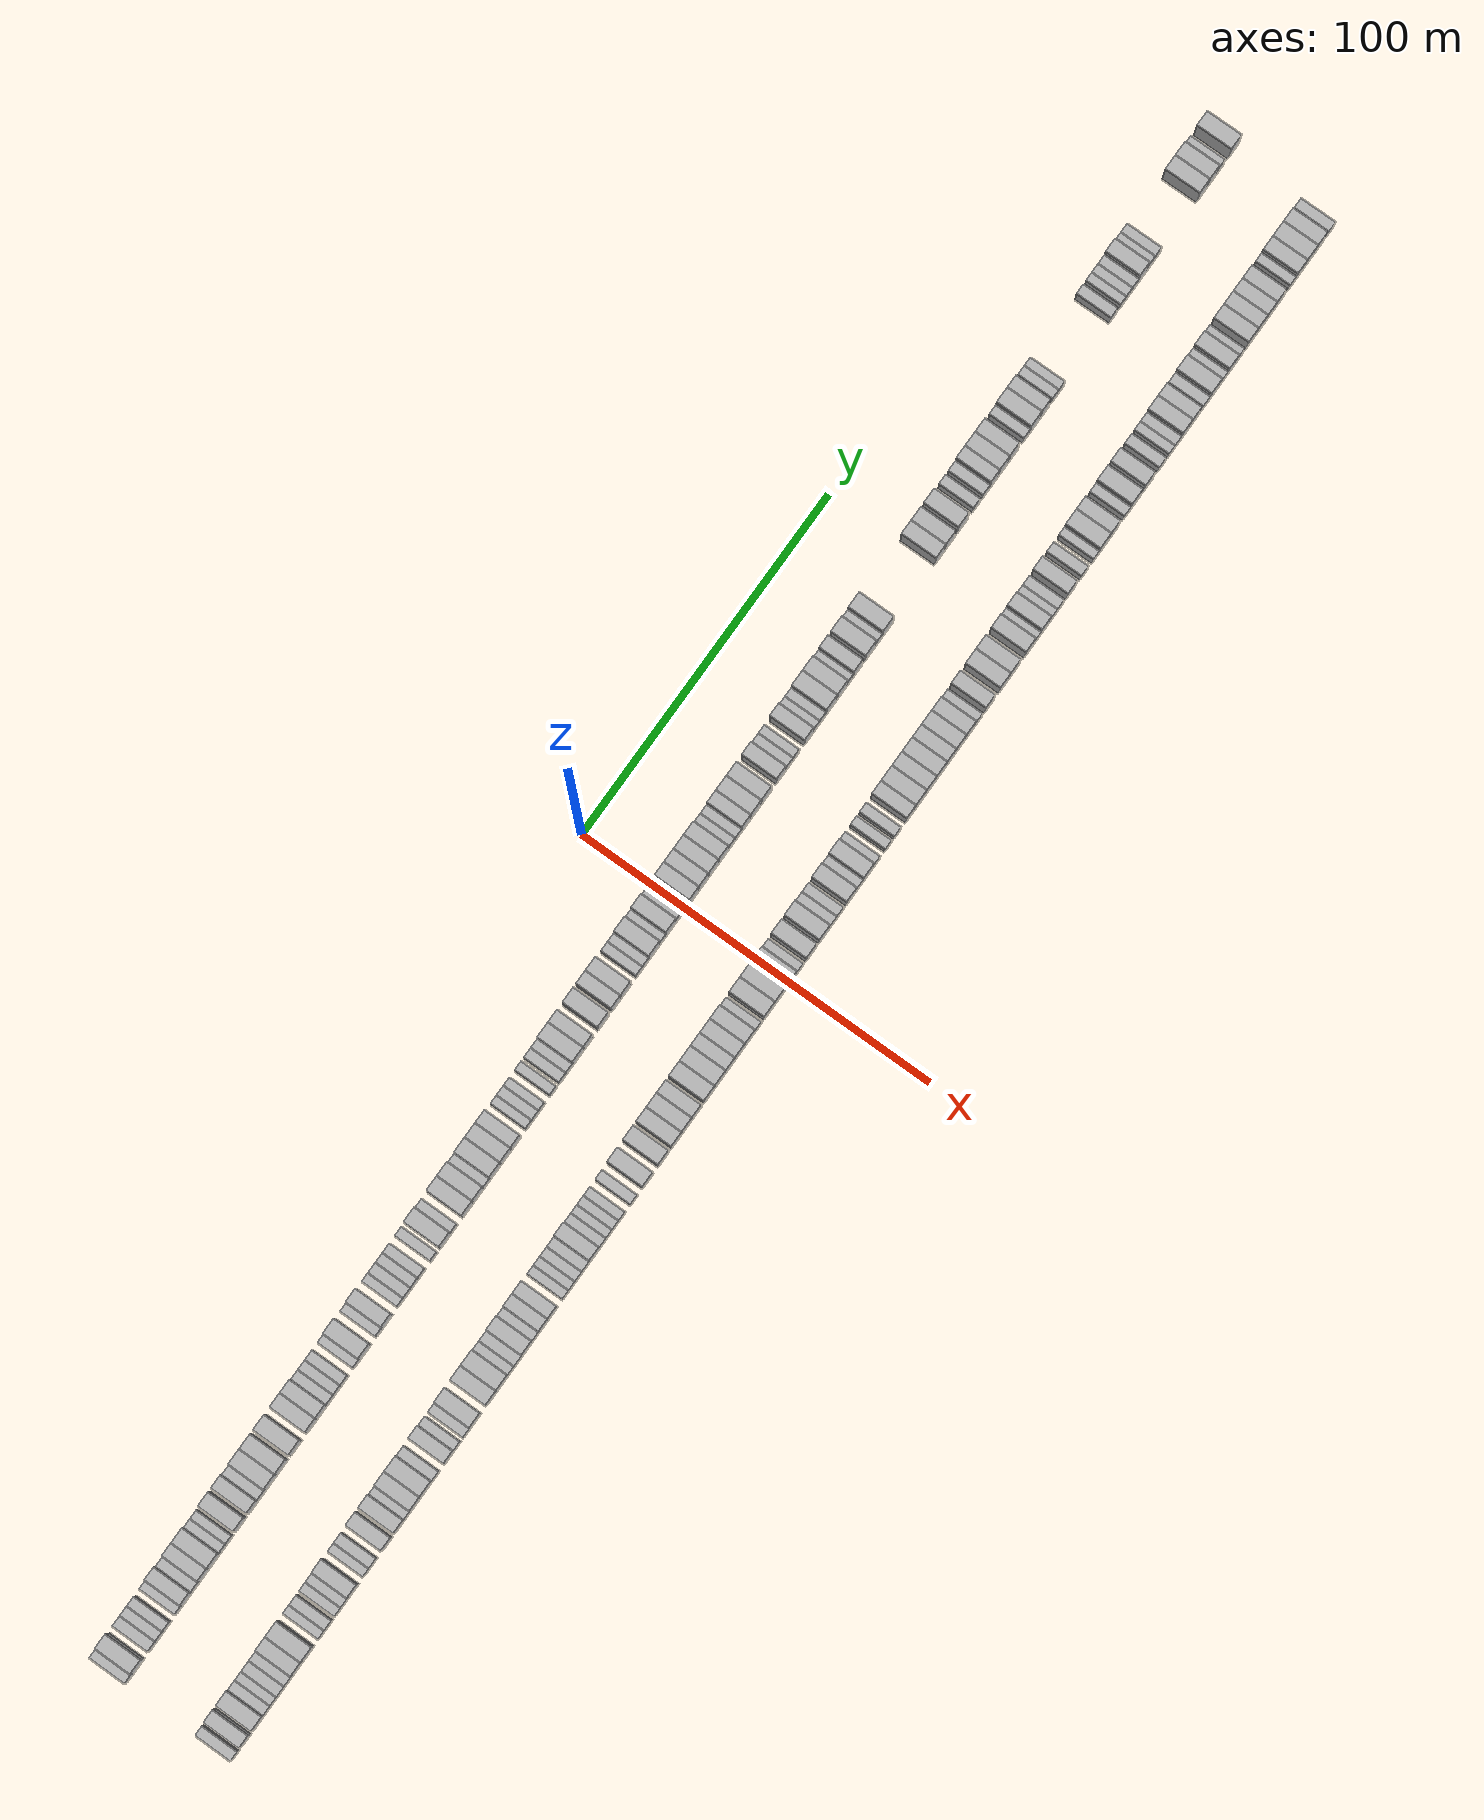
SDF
<sdf version="1.6">
 <world name="default">
  <scene>
   <sky><clouds><speed>12</speed></clouds></sky>
   <ambient>0.4 0.4 0.4 1</ambient>
   <background>0.7 0.7 0.7 1</background>
   <shadows>1</shadows>
  </scene>
  <gravity>0 0 -9.8066</gravity>
  <magnetic_field>6e-06 2.3e-05 -4.2e-05</magnetic_field>
  <physics default="0" name="default_physics" type="ode">
   <ode>
    <solver>
     <type>quick</type>
     <iters>10</iters>
     <sor>1.0</sor>
     <use_dynamic_moi_rescaling>0</use_dynamic_moi_rescaling>
    </solver>
    <constraints>
     <cfm>0</cfm>
     <erp>0.2</erp>
     <contact_max_correcting_vel>100</contact_max_correcting_vel>
     <contact_surface_layer>0.001</contact_surface_layer>
    </constraints>
   </ode>
   <max_step_size>0.004</max_step_size>
   <real_time_factor>1</real_time_factor>
   <real_time_update_rate>250</real_time_update_rate>
  </physics>
  <light name="sun" type="directional">
   <pose>0 0 10 0 0 0</pose>
   <diffuse>0.8 0.8 0.8 1</diffuse>
   <specular>0.2 0.2 0.2 1</specular>
   <attenuation>
    <range>1000</range>
    <constant>0.9</constant>
    <linear>0.01</linear>
    <quadratic>0.001</quadratic>
   </attenuation>
   <direction>-0.5 0.1 -0.9</direction>
  </light>
  <model name="building_1">
   <static>1</static>
   <pose>25.0000 -218.6373 0 0.000000 0.000000 0.000000</pose>
   <link name="link">
    <pose>0 0 3.00 0 0 0</pose>
    <collision name="collision"><geometry><box><size>10.0000 2.7254 6.0000</size></box></geometry></collision>
    <visual name="visual">
     <cast_shadows>0</cast_shadows>
     <geometry><box><size>10.0000 2.7254 6.0000</size></box></geometry>
     <material>
      <script>
       <uri>model://HANNAS_wall/materials/scripts</uri>
       <uri>model://HANNAS_wall/materials/textures</uri>
       <name>vrc/HANNAS_wall</name>
      </script>
     </material>
    </visual>
   </link>
  </model>
  <model name="building_2">
   <static>1</static>
   <pose>25.0000 -215.2229 0 0.000000 0.000000 0.000000</pose>
   <link name="link">
    <pose>0 0 4.50 0 0 0</pose>
    <collision name="collision"><geometry><box><size>10.0000 4.1034 9.0000</size></box></geometry></collision>
    <visual name="visual">
     <cast_shadows>0</cast_shadows>
     <geometry><box><size>10.0000 4.1034 9.0000</size></box></geometry>
     <material>
      <script>
       <uri>model://HANNAS_wall/materials/scripts</uri>
       <uri>model://HANNAS_wall/materials/textures</uri>
       <name>vrc/HANNAS_wall</name>
      </script>
     </material>
    </visual>
   </link>
  </model>
  <model name="building_3">
   <static>1</static>
   <pose>25.0000 -209.6990 0 0.000000 0.000000 0.000000</pose>
   <link name="link">
    <pose>0 0 3.00 0 0 0</pose>
    <collision name="collision"><geometry><box><size>10.0000 2.9444 6.0000</size></box></geometry></collision>
    <visual name="visual">
     <cast_shadows>0</cast_shadows>
     <geometry><box><size>10.0000 2.9444 6.0000</size></box></geometry>
     <material>
      <script>
       <uri>model://HANNAS_wall/materials/scripts</uri>
       <uri>model://HANNAS_wall/materials/textures</uri>
       <name>vrc/HANNAS_wall</name>
      </script>
     </material>
    </visual>
   </link>
  </model>
  <model name="building_4">
   <static>1</static>
   <pose>25.0000 -206.8797 0 0.000000 0.000000 0.000000</pose>
   <link name="link">
    <pose>0 0 3.00 0 0 0</pose>
    <collision name="collision"><geometry><box><size>10.0000 2.6942 6.0000</size></box></geometry></collision>
    <visual name="visual">
     <cast_shadows>0</cast_shadows>
     <geometry><box><size>10.0000 2.6942 6.0000</size></box></geometry>
     <material>
      <script>
       <uri>model://HANNAS_wall/materials/scripts</uri>
       <uri>model://HANNAS_wall/materials/textures</uri>
       <name>vrc/HANNAS_wall</name>
      </script>
     </material>
    </visual>
   </link>
  </model>
  <model name="building_5">
   <static>1</static>
   <pose>25.0000 -204.1767 0 0.000000 0.000000 0.000000</pose>
   <link name="link">
    <pose>0 0 3.00 0 0 0</pose>
    <collision name="collision"><geometry><box><size>10.0000 2.7119 6.0000</size></box></geometry></collision>
    <visual name="visual">
     <cast_shadows>0</cast_shadows>
     <geometry><box><size>10.0000 2.7119 6.0000</size></box></geometry>
     <material>
      <script>
       <uri>model://HANNAS_wall/materials/scripts</uri>
       <uri>model://HANNAS_wall/materials/textures</uri>
       <name>vrc/HANNAS_wall</name>
      </script>
     </material>
    </visual>
   </link>
  </model>
  <model name="building_6">
   <static>1</static>
   <pose>25.0000 -199.5286 0 0.000000 0.000000 0.000000</pose>
   <link name="link">
    <pose>0 0 3.00 0 0 0</pose>
    <collision name="collision"><geometry><box><size>10.0000 2.5842 6.0000</size></box></geometry></collision>
    <visual name="visual">
     <cast_shadows>0</cast_shadows>
     <geometry><box><size>10.0000 2.5842 6.0000</size></box></geometry>
     <material>
      <script>
       <uri>model://HANNAS_wall/materials/scripts</uri>
       <uri>model://HANNAS_wall/materials/textures</uri>
       <name>vrc/HANNAS_wall</name>
      </script>
     </material>
    </visual>
   </link>
  </model>
  <model name="building_7">
   <static>1</static>
   <pose>25.0000 -196.3921 0 0.000000 0.000000 0.000000</pose>
   <link name="link">
    <pose>0 0 4.50 0 0 0</pose>
    <collision name="collision"><geometry><box><size>10.0000 3.6888 9.0000</size></box></geometry></collision>
    <visual name="visual">
     <cast_shadows>0</cast_shadows>
     <geometry><box><size>10.0000 3.6888 9.0000</size></box></geometry>
     <material>
      <script>
       <uri>model://HANNAS_wall/materials/scripts</uri>
       <uri>model://HANNAS_wall/materials/textures</uri>
       <name>vrc/HANNAS_wall</name>
      </script>
     </material>
    </visual>
   </link>
  </model>
  <model name="building_8">
   <static>1</static>
   <pose>25.0000 -193.0513 0 0.000000 0.000000 0.000000</pose>
   <link name="link">
    <pose>0 0 3.00 0 0 0</pose>
    <collision name="collision"><geometry><box><size>10.0000 2.9928 6.0000</size></box></geometry></collision>
    <visual name="visual">
     <cast_shadows>0</cast_shadows>
     <geometry><box><size>10.0000 2.9928 6.0000</size></box></geometry>
     <material>
      <script>
       <uri>model://HANNAS_wall/materials/scripts</uri>
       <uri>model://HANNAS_wall/materials/textures</uri>
       <name>vrc/HANNAS_wall</name>
      </script>
     </material>
    </visual>
   </link>
  </model>
  <model name="building_9">
   <static>1</static>
   <pose>25.0000 -189.7349 0 0.000000 0.000000 0.000000</pose>
   <link name="link">
    <pose>0 0 4.50 0 0 0</pose>
    <collision name="collision"><geometry><box><size>10.0000 3.6400 9.0000</size></box></geometry></collision>
    <visual name="visual">
     <cast_shadows>0</cast_shadows>
     <geometry><box><size>10.0000 3.6400 9.0000</size></box></geometry>
     <material>
      <script>
       <uri>model://HANNAS_wall/materials/scripts</uri>
       <uri>model://HANNAS_wall/materials/textures</uri>
       <name>vrc/HANNAS_wall</name>
      </script>
     </material>
    </visual>
   </link>
  </model>
  <model name="building_10">
   <static>1</static>
   <pose>25.0000 -185.7812 0 0.000000 0.000000 0.000000</pose>
   <link name="link">
    <pose>0 0 4.50 0 0 0</pose>
    <collision name="collision"><geometry><box><size>10.0000 4.2674 9.0000</size></box></geometry></collision>
    <visual name="visual">
     <cast_shadows>0</cast_shadows>
     <geometry><box><size>10.0000 4.2674 9.0000</size></box></geometry>
     <material>
      <script>
       <uri>model://HANNAS_wall/materials/scripts</uri>
       <uri>model://HANNAS_wall/materials/textures</uri>
       <name>vrc/HANNAS_wall</name>
      </script>
     </material>
    </visual>
   </link>
  </model>
  <model name="building_11">
   <static>1</static>
   <pose>25.0000 -182.3997 0 0.000000 0.000000 0.000000</pose>
   <link name="link">
    <pose>0 0 3.00 0 0 0</pose>
    <collision name="collision"><geometry><box><size>10.0000 2.4958 6.0000</size></box></geometry></collision>
    <visual name="visual">
     <cast_shadows>0</cast_shadows>
     <geometry><box><size>10.0000 2.4958 6.0000</size></box></geometry>
     <material>
      <script>
       <uri>model://HANNAS_wall/materials/scripts</uri>
       <uri>model://HANNAS_wall/materials/textures</uri>
       <name>vrc/HANNAS_wall</name>
      </script>
     </material>
    </visual>
   </link>
  </model>
  <model name="building_12">
   <static>1</static>
   <pose>25.0000 -179.9335 0 0.000000 0.000000 0.000000</pose>
   <link name="link">
    <pose>0 0 3.00 0 0 0</pose>
    <collision name="collision"><geometry><box><size>10.0000 2.4366 6.0000</size></box></geometry></collision>
    <visual name="visual">
     <cast_shadows>0</cast_shadows>
     <geometry><box><size>10.0000 2.4366 6.0000</size></box></geometry>
     <material>
      <script>
       <uri>model://HANNAS_wall/materials/scripts</uri>
       <uri>model://HANNAS_wall/materials/textures</uri>
       <name>vrc/HANNAS_wall</name>
      </script>
     </material>
    </visual>
   </link>
  </model>
  <model name="building_13">
   <static>1</static>
   <pose>25.0000 -175.6765 0 0.000000 0.000000 0.000000</pose>
   <link name="link">
    <pose>0 0 4.50 0 0 0</pose>
    <collision name="collision"><geometry><box><size>10.0000 4.0773 9.0000</size></box></geometry></collision>
    <visual name="visual">
     <cast_shadows>0</cast_shadows>
     <geometry><box><size>10.0000 4.0773 9.0000</size></box></geometry>
     <material>
      <script>
       <uri>model://HANNAS_wall/materials/scripts</uri>
       <uri>model://HANNAS_wall/materials/textures</uri>
       <name>vrc/HANNAS_wall</name>
      </script>
     </material>
    </visual>
   </link>
  </model>
  <model name="building_14">
   <static>1</static>
   <pose>25.0000 -170.7742 0 0.000000 0.000000 0.000000</pose>
   <link name="link">
    <pose>0 0 4.50 0 0 0</pose>
    <collision name="collision"><geometry><box><size>10.0000 3.7273 9.0000</size></box></geometry></collision>
    <visual name="visual">
     <cast_shadows>0</cast_shadows>
     <geometry><box><size>10.0000 3.7273 9.0000</size></box></geometry>
     <material>
      <script>
       <uri>model://HANNAS_wall/materials/scripts</uri>
       <uri>model://HANNAS_wall/materials/textures</uri>
       <name>vrc/HANNAS_wall</name>
      </script>
     </material>
    </visual>
   </link>
  </model>
  <model name="building_15">
   <static>1</static>
   <pose>25.0000 -167.4381 0 0.000000 0.000000 0.000000</pose>
   <link name="link">
    <pose>0 0 3.00 0 0 0</pose>
    <collision name="collision"><geometry><box><size>10.0000 2.9449 6.0000</size></box></geometry></collision>
    <visual name="visual">
     <cast_shadows>0</cast_shadows>
     <geometry><box><size>10.0000 2.9449 6.0000</size></box></geometry>
     <material>
      <script>
       <uri>model://HANNAS_wall/materials/scripts</uri>
       <uri>model://HANNAS_wall/materials/textures</uri>
       <name>vrc/HANNAS_wall</name>
      </script>
     </material>
    </visual>
   </link>
  </model>
  <model name="building_16">
   <static>1</static>
   <pose>25.0000 -163.7982 0 0.000000 0.000000 0.000000</pose>
   <link name="link">
    <pose>0 0 4.50 0 0 0</pose>
    <collision name="collision"><geometry><box><size>10.0000 4.3349 9.0000</size></box></geometry></collision>
    <visual name="visual">
     <cast_shadows>0</cast_shadows>
     <geometry><box><size>10.0000 4.3349 9.0000</size></box></geometry>
     <material>
      <script>
       <uri>model://HANNAS_wall/materials/scripts</uri>
       <uri>model://HANNAS_wall/materials/textures</uri>
       <name>vrc/HANNAS_wall</name>
      </script>
     </material>
    </visual>
   </link>
  </model>
  <model name="building_17">
   <static>1</static>
   <pose>25.0000 -159.5141 0 0.000000 0.000000 0.000000</pose>
   <link name="link">
    <pose>0 0 4.50 0 0 0</pose>
    <collision name="collision"><geometry><box><size>10.0000 4.2334 9.0000</size></box></geometry></collision>
    <visual name="visual">
     <cast_shadows>0</cast_shadows>
     <geometry><box><size>10.0000 4.2334 9.0000</size></box></geometry>
     <material>
      <script>
       <uri>model://HANNAS_wall/materials/scripts</uri>
       <uri>model://HANNAS_wall/materials/textures</uri>
       <name>vrc/HANNAS_wall</name>
      </script>
     </material>
    </visual>
   </link>
  </model>
  <model name="building_18">
   <static>1</static>
   <pose>25.0000 -154.1911 0 0.000000 0.000000 0.000000</pose>
   <link name="link">
    <pose>0 0 4.50 0 0 0</pose>
    <collision name="collision"><geometry><box><size>10.0000 4.4124 9.0000</size></box></geometry></collision>
    <visual name="visual">
     <cast_shadows>0</cast_shadows>
     <geometry><box><size>10.0000 4.4124 9.0000</size></box></geometry>
     <material>
      <script>
       <uri>model://HANNAS_wall/materials/scripts</uri>
       <uri>model://HANNAS_wall/materials/textures</uri>
       <name>vrc/HANNAS_wall</name>
      </script>
     </material>
    </visual>
   </link>
  </model>
  <model name="building_19">
   <static>1</static>
   <pose>25.0000 -147.9562 0 0.000000 0.000000 0.000000</pose>
   <link name="link">
    <pose>0 0 4.50 0 0 0</pose>
    <collision name="collision"><geometry><box><size>10.0000 4.0575 9.0000</size></box></geometry></collision>
    <visual name="visual">
     <cast_shadows>0</cast_shadows>
     <geometry><box><size>10.0000 4.0575 9.0000</size></box></geometry>
     <material>
      <script>
       <uri>model://HANNAS_wall/materials/scripts</uri>
       <uri>model://HANNAS_wall/materials/textures</uri>
       <name>vrc/HANNAS_wall</name>
      </script>
     </material>
    </visual>
   </link>
  </model>
  <model name="building_20">
   <static>1</static>
   <pose>25.0000 -144.0206 0 0.000000 0.000000 0.000000</pose>
   <link name="link">
    <pose>0 0 4.50 0 0 0</pose>
    <collision name="collision"><geometry><box><size>10.0000 3.8136 9.0000</size></box></geometry></collision>
    <visual name="visual">
     <cast_shadows>0</cast_shadows>
     <geometry><box><size>10.0000 3.8136 9.0000</size></box></geometry>
     <material>
      <script>
       <uri>model://HANNAS_wall/materials/scripts</uri>
       <uri>model://HANNAS_wall/materials/textures</uri>
       <name>vrc/HANNAS_wall</name>
      </script>
     </material>
    </visual>
   </link>
  </model>
  <model name="building_21">
   <static>1</static>
   <pose>25.0000 -140.7175 0 0.000000 0.000000 0.000000</pose>
   <link name="link">
    <pose>0 0 3.00 0 0 0</pose>
    <collision name="collision"><geometry><box><size>10.0000 2.7927 6.0000</size></box></geometry></collision>
    <visual name="visual">
     <cast_shadows>0</cast_shadows>
     <geometry><box><size>10.0000 2.7927 6.0000</size></box></geometry>
     <material>
      <script>
       <uri>model://HANNAS_wall/materials/scripts</uri>
       <uri>model://HANNAS_wall/materials/textures</uri>
       <name>vrc/HANNAS_wall</name>
      </script>
     </material>
    </visual>
   </link>
  </model>
  <model name="building_22">
   <static>1</static>
   <pose>25.0000 -137.9594 0 0.000000 0.000000 0.000000</pose>
   <link name="link">
    <pose>0 0 3.00 0 0 0</pose>
    <collision name="collision"><geometry><box><size>10.0000 2.7236 6.0000</size></box></geometry></collision>
    <visual name="visual">
     <cast_shadows>0</cast_shadows>
     <geometry><box><size>10.0000 2.7236 6.0000</size></box></geometry>
     <material>
      <script>
       <uri>model://HANNAS_wall/materials/scripts</uri>
       <uri>model://HANNAS_wall/materials/textures</uri>
       <name>vrc/HANNAS_wall</name>
      </script>
     </material>
    </visual>
   </link>
  </model>
  <model name="building_23">
   <static>1</static>
   <pose>25.0000 -135.1824 0 0.000000 0.000000 0.000000</pose>
   <link name="link">
    <pose>0 0 3.00 0 0 0</pose>
    <collision name="collision"><geometry><box><size>10.0000 2.8303 6.0000</size></box></geometry></collision>
    <visual name="visual">
     <cast_shadows>0</cast_shadows>
     <geometry><box><size>10.0000 2.8303 6.0000</size></box></geometry>
     <material>
      <script>
       <uri>model://HANNAS_wall/materials/scripts</uri>
       <uri>model://HANNAS_wall/materials/textures</uri>
       <name>vrc/HANNAS_wall</name>
      </script>
     </material>
    </visual>
   </link>
  </model>
  <model name="building_24">
   <static>1</static>
   <pose>25.0000 -130.5386 0 0.000000 0.000000 0.000000</pose>
   <link name="link">
    <pose>0 0 3.00 0 0 0</pose>
    <collision name="collision"><geometry><box><size>10.0000 2.4573 6.0000</size></box></geometry></collision>
    <visual name="visual">
     <cast_shadows>0</cast_shadows>
     <geometry><box><size>10.0000 2.4573 6.0000</size></box></geometry>
     <material>
      <script>
       <uri>model://HANNAS_wall/materials/scripts</uri>
       <uri>model://HANNAS_wall/materials/textures</uri>
       <name>vrc/HANNAS_wall</name>
      </script>
     </material>
    </visual>
   </link>
  </model>
  <model name="building_25">
   <static>1</static>
   <pose>25.0000 -127.1164 0 0.000000 0.000000 0.000000</pose>
   <link name="link">
    <pose>0 0 4.50 0 0 0</pose>
    <collision name="collision"><geometry><box><size>10.0000 4.3872 9.0000</size></box></geometry></collision>
    <visual name="visual">
     <cast_shadows>0</cast_shadows>
     <geometry><box><size>10.0000 4.3872 9.0000</size></box></geometry>
     <material>
      <script>
       <uri>model://HANNAS_wall/materials/scripts</uri>
       <uri>model://HANNAS_wall/materials/textures</uri>
       <name>vrc/HANNAS_wall</name>
      </script>
     </material>
    </visual>
   </link>
  </model>
  <model name="building_26">
   <static>1</static>
   <pose>25.0000 -121.6655 0 0.000000 0.000000 0.000000</pose>
   <link name="link">
    <pose>0 0 3.00 0 0 0</pose>
    <collision name="collision"><geometry><box><size>10.0000 2.5145 6.0000</size></box></geometry></collision>
    <visual name="visual">
     <cast_shadows>0</cast_shadows>
     <geometry><box><size>10.0000 2.5145 6.0000</size></box></geometry>
     <material>
      <script>
       <uri>model://HANNAS_wall/materials/scripts</uri>
       <uri>model://HANNAS_wall/materials/textures</uri>
       <name>vrc/HANNAS_wall</name>
      </script>
     </material>
    </visual>
   </link>
  </model>
  <model name="building_27">
   <static>1</static>
   <pose>25.0000 -118.4431 0 0.000000 0.000000 0.000000</pose>
   <link name="link">
    <pose>0 0 4.50 0 0 0</pose>
    <collision name="collision"><geometry><box><size>10.0000 3.9304 9.0000</size></box></geometry></collision>
    <visual name="visual">
     <cast_shadows>0</cast_shadows>
     <geometry><box><size>10.0000 3.9304 9.0000</size></box></geometry>
     <material>
      <script>
       <uri>model://HANNAS_wall/materials/scripts</uri>
       <uri>model://HANNAS_wall/materials/textures</uri>
       <name>vrc/HANNAS_wall</name>
      </script>
     </material>
    </visual>
   </link>
  </model>
  <model name="building_28">
   <static>1</static>
   <pose>25.0000 -113.2305 0 0.000000 0.000000 0.000000</pose>
   <link name="link">
    <pose>0 0 3.00 0 0 0</pose>
    <collision name="collision"><geometry><box><size>10.0000 2.4947 6.0000</size></box></geometry></collision>
    <visual name="visual">
     <cast_shadows>0</cast_shadows>
     <geometry><box><size>10.0000 2.4947 6.0000</size></box></geometry>
     <material>
      <script>
       <uri>model://HANNAS_wall/materials/scripts</uri>
       <uri>model://HANNAS_wall/materials/textures</uri>
       <name>vrc/HANNAS_wall</name>
      </script>
     </material>
    </visual>
   </link>
  </model>
  <model name="building_29">
   <static>1</static>
   <pose>25.0000 -110.5142 0 0.000000 0.000000 0.000000</pose>
   <link name="link">
    <pose>0 0 3.00 0 0 0</pose>
    <collision name="collision"><geometry><box><size>10.0000 2.9378 6.0000</size></box></geometry></collision>
    <visual name="visual">
     <cast_shadows>0</cast_shadows>
     <geometry><box><size>10.0000 2.9378 6.0000</size></box></geometry>
     <material>
      <script>
       <uri>model://HANNAS_wall/materials/scripts</uri>
       <uri>model://HANNAS_wall/materials/textures</uri>
       <name>vrc/HANNAS_wall</name>
      </script>
     </material>
    </visual>
   </link>
  </model>
  <model name="building_30">
   <static>1</static>
   <pose>25.0000 -107.6728 0 0.000000 0.000000 0.000000</pose>
   <link name="link">
    <pose>0 0 3.00 0 0 0</pose>
    <collision name="collision"><geometry><box><size>10.0000 2.7450 6.0000</size></box></geometry></collision>
    <visual name="visual">
     <cast_shadows>0</cast_shadows>
     <geometry><box><size>10.0000 2.7450 6.0000</size></box></geometry>
     <material>
      <script>
       <uri>model://HANNAS_wall/materials/scripts</uri>
       <uri>model://HANNAS_wall/materials/textures</uri>
       <name>vrc/HANNAS_wall</name>
      </script>
     </material>
    </visual>
   </link>
  </model>
  <model name="building_31">
   <static>1</static>
   <pose>25.0000 -104.9131 0 0.000000 0.000000 0.000000</pose>
   <link name="link">
    <pose>0 0 3.00 0 0 0</pose>
    <collision name="collision"><geometry><box><size>10.0000 2.7745 6.0000</size></box></geometry></collision>
    <visual name="visual">
     <cast_shadows>0</cast_shadows>
     <geometry><box><size>10.0000 2.7745 6.0000</size></box></geometry>
     <material>
      <script>
       <uri>model://HANNAS_wall/materials/scripts</uri>
       <uri>model://HANNAS_wall/materials/textures</uri>
       <name>vrc/HANNAS_wall</name>
      </script>
     </material>
    </visual>
   </link>
  </model>
  <model name="building_32">
   <static>1</static>
   <pose>25.0000 -100.1636 0 0.000000 0.000000 0.000000</pose>
   <link name="link">
    <pose>0 0 3.00 0 0 0</pose>
    <collision name="collision"><geometry><box><size>10.0000 2.7245 6.0000</size></box></geometry></collision>
    <visual name="visual">
     <cast_shadows>0</cast_shadows>
     <geometry><box><size>10.0000 2.7245 6.0000</size></box></geometry>
     <material>
      <script>
       <uri>model://HANNAS_wall/materials/scripts</uri>
       <uri>model://HANNAS_wall/materials/textures</uri>
       <name>vrc/HANNAS_wall</name>
      </script>
     </material>
    </visual>
   </link>
  </model>
  <model name="building_33">
   <static>1</static>
   <pose>25.0000 -95.6585 0 0.000000 0.000000 0.000000</pose>
   <link name="link">
    <pose>0 0 4.50 0 0 0</pose>
    <collision name="collision"><geometry><box><size>10.0000 4.2858 9.0000</size></box></geometry></collision>
    <visual name="visual">
     <cast_shadows>0</cast_shadows>
     <geometry><box><size>10.0000 4.2858 9.0000</size></box></geometry>
     <material>
      <script>
       <uri>model://HANNAS_wall/materials/scripts</uri>
       <uri>model://HANNAS_wall/materials/textures</uri>
       <name>vrc/HANNAS_wall</name>
      </script>
     </material>
    </visual>
   </link>
  </model>
  <model name="building_34">
   <static>1</static>
   <pose>25.0000 -92.2203 0 0.000000 0.000000 0.000000</pose>
   <link name="link">
    <pose>0 0 3.00 0 0 0</pose>
    <collision name="collision"><geometry><box><size>10.0000 2.5905 6.0000</size></box></geometry></collision>
    <visual name="visual">
     <cast_shadows>0</cast_shadows>
     <geometry><box><size>10.0000 2.5905 6.0000</size></box></geometry>
     <material>
      <script>
       <uri>model://HANNAS_wall/materials/scripts</uri>
       <uri>model://HANNAS_wall/materials/textures</uri>
       <name>vrc/HANNAS_wall</name>
      </script>
     </material>
    </visual>
   </link>
  </model>
  <model name="building_35">
   <static>1</static>
   <pose>25.0000 -86.7971 0 0.000000 0.000000 0.000000</pose>
   <link name="link">
    <pose>0 0 4.50 0 0 0</pose>
    <collision name="collision"><geometry><box><size>10.0000 4.2560 9.0000</size></box></geometry></collision>
    <visual name="visual">
     <cast_shadows>0</cast_shadows>
     <geometry><box><size>10.0000 4.2560 9.0000</size></box></geometry>
     <material>
      <script>
       <uri>model://HANNAS_wall/materials/scripts</uri>
       <uri>model://HANNAS_wall/materials/textures</uri>
       <name>vrc/HANNAS_wall</name>
      </script>
     </material>
    </visual>
   </link>
  </model>
  <model name="building_36">
   <static>1</static>
   <pose>25.0000 -82.6416 0 0.000000 0.000000 0.000000</pose>
   <link name="link">
    <pose>0 0 4.50 0 0 0</pose>
    <collision name="collision"><geometry><box><size>10.0000 4.0550 9.0000</size></box></geometry></collision>
    <visual name="visual">
     <cast_shadows>0</cast_shadows>
     <geometry><box><size>10.0000 4.0550 9.0000</size></box></geometry>
     <material>
      <script>
       <uri>model://HANNAS_wall/materials/scripts</uri>
       <uri>model://HANNAS_wall/materials/textures</uri>
       <name>vrc/HANNAS_wall</name>
      </script>
     </material>
    </visual>
   </link>
  </model>
  <model name="building_37">
   <static>1</static>
   <pose>25.0000 -79.3281 0 0.000000 0.000000 0.000000</pose>
   <link name="link">
    <pose>0 0 3.00 0 0 0</pose>
    <collision name="collision"><geometry><box><size>10.0000 2.5721 6.0000</size></box></geometry></collision>
    <visual name="visual">
     <cast_shadows>0</cast_shadows>
     <geometry><box><size>10.0000 2.5721 6.0000</size></box></geometry>
     <material>
      <script>
       <uri>model://HANNAS_wall/materials/scripts</uri>
       <uri>model://HANNAS_wall/materials/textures</uri>
       <name>vrc/HANNAS_wall</name>
      </script>
     </material>
    </visual>
   </link>
  </model>
  <model name="building_38">
   <static>1</static>
   <pose>25.0000 -75.8928 0 0.000000 0.000000 0.000000</pose>
   <link name="link">
    <pose>0 0 4.50 0 0 0</pose>
    <collision name="collision"><geometry><box><size>10.0000 4.2985 9.0000</size></box></geometry></collision>
    <visual name="visual">
     <cast_shadows>0</cast_shadows>
     <geometry><box><size>10.0000 4.2985 9.0000</size></box></geometry>
     <material>
      <script>
       <uri>model://HANNAS_wall/materials/scripts</uri>
       <uri>model://HANNAS_wall/materials/textures</uri>
       <name>vrc/HANNAS_wall</name>
      </script>
     </material>
    </visual>
   </link>
  </model>
  <model name="building_39">
   <static>1</static>
   <pose>25.0000 -71.6768 0 0.000000 0.000000 0.000000</pose>
   <link name="link">
    <pose>0 0 4.50 0 0 0</pose>
    <collision name="collision"><geometry><box><size>10.0000 4.1334 9.0000</size></box></geometry></collision>
    <visual name="visual">
     <cast_shadows>0</cast_shadows>
     <geometry><box><size>10.0000 4.1334 9.0000</size></box></geometry>
     <material>
      <script>
       <uri>model://HANNAS_wall/materials/scripts</uri>
       <uri>model://HANNAS_wall/materials/textures</uri>
       <name>vrc/HANNAS_wall</name>
      </script>
     </material>
    </visual>
   </link>
  </model>
  <model name="building_40">
   <static>1</static>
   <pose>25.0000 -67.7535 0 0.000000 0.000000 0.000000</pose>
   <link name="link">
    <pose>0 0 4.50 0 0 0</pose>
    <collision name="collision"><geometry><box><size>10.0000 3.7132 9.0000</size></box></geometry></collision>
    <visual name="visual">
     <cast_shadows>0</cast_shadows>
     <geometry><box><size>10.0000 3.7132 9.0000</size></box></geometry>
     <material>
      <script>
       <uri>model://HANNAS_wall/materials/scripts</uri>
       <uri>model://HANNAS_wall/materials/textures</uri>
       <name>vrc/HANNAS_wall</name>
      </script>
     </material>
    </visual>
   </link>
  </model>
  <model name="building_41">
   <static>1</static>
   <pose>25.0000 -62.6704 0 0.000000 0.000000 0.000000</pose>
   <link name="link">
    <pose>0 0 3.00 0 0 0</pose>
    <collision name="collision"><geometry><box><size>10.0000 2.4529 6.0000</size></box></geometry></collision>
    <visual name="visual">
     <cast_shadows>0</cast_shadows>
     <geometry><box><size>10.0000 2.4529 6.0000</size></box></geometry>
     <material>
      <script>
       <uri>model://HANNAS_wall/materials/scripts</uri>
       <uri>model://HANNAS_wall/materials/textures</uri>
       <name>vrc/HANNAS_wall</name>
      </script>
     </material>
    </visual>
   </link>
  </model>
  <model name="building_42">
   <static>1</static>
   <pose>25.0000 -60.0665 0 0.000000 0.000000 0.000000</pose>
   <link name="link">
    <pose>0 0 3.00 0 0 0</pose>
    <collision name="collision"><geometry><box><size>10.0000 2.7548 6.0000</size></box></geometry></collision>
    <visual name="visual">
     <cast_shadows>0</cast_shadows>
     <geometry><box><size>10.0000 2.7548 6.0000</size></box></geometry>
     <material>
      <script>
       <uri>model://HANNAS_wall/materials/scripts</uri>
       <uri>model://HANNAS_wall/materials/textures</uri>
       <name>vrc/HANNAS_wall</name>
      </script>
     </material>
    </visual>
   </link>
  </model>
  <model name="building_43">
   <static>1</static>
   <pose>25.0000 -57.4870 0 0.000000 0.000000 0.000000</pose>
   <link name="link">
    <pose>0 0 3.00 0 0 0</pose>
    <collision name="collision"><geometry><box><size>10.0000 2.4043 6.0000</size></box></geometry></collision>
    <visual name="visual">
     <cast_shadows>0</cast_shadows>
     <geometry><box><size>10.0000 2.4043 6.0000</size></box></geometry>
     <material>
      <script>
       <uri>model://HANNAS_wall/materials/scripts</uri>
       <uri>model://HANNAS_wall/materials/textures</uri>
       <name>vrc/HANNAS_wall</name>
      </script>
     </material>
    </visual>
   </link>
  </model>
  <model name="building_44">
   <static>1</static>
   <pose>25.0000 -52.9829 0 0.000000 0.000000 0.000000</pose>
   <link name="link">
    <pose>0 0 3.00 0 0 0</pose>
    <collision name="collision"><geometry><box><size>10.0000 2.6038 6.0000</size></box></geometry></collision>
    <visual name="visual">
     <cast_shadows>0</cast_shadows>
     <geometry><box><size>10.0000 2.6038 6.0000</size></box></geometry>
     <material>
      <script>
       <uri>model://HANNAS_wall/materials/scripts</uri>
       <uri>model://HANNAS_wall/materials/textures</uri>
       <name>vrc/HANNAS_wall</name>
      </script>
     </material>
    </visual>
   </link>
  </model>
  <model name="building_45">
   <static>1</static>
   <pose>25.0000 -49.2864 0 0.000000 0.000000 0.000000</pose>
   <link name="link">
    <pose>0 0 3.00 0 0 0</pose>
    <collision name="collision"><geometry><box><size>10.0000 2.7891 6.0000</size></box></geometry></collision>
    <visual name="visual">
     <cast_shadows>0</cast_shadows>
     <geometry><box><size>10.0000 2.7891 6.0000</size></box></geometry>
     <material>
      <script>
       <uri>model://HANNAS_wall/materials/scripts</uri>
       <uri>model://HANNAS_wall/materials/textures</uri>
       <name>vrc/HANNAS_wall</name>
      </script>
     </material>
    </visual>
   </link>
  </model>
  <model name="building_46">
   <static>1</static>
   <pose>25.0000 -46.5743 0 0.000000 0.000000 0.000000</pose>
   <link name="link">
    <pose>0 0 3.00 0 0 0</pose>
    <collision name="collision"><geometry><box><size>10.0000 2.6351 6.0000</size></box></geometry></collision>
    <visual name="visual">
     <cast_shadows>0</cast_shadows>
     <geometry><box><size>10.0000 2.6351 6.0000</size></box></geometry>
     <material>
      <script>
       <uri>model://HANNAS_wall/materials/scripts</uri>
       <uri>model://HANNAS_wall/materials/textures</uri>
       <name>vrc/HANNAS_wall</name>
      </script>
     </material>
    </visual>
   </link>
  </model>
  <model name="building_47">
   <static>1</static>
   <pose>25.0000 -43.0862 0 0.000000 0.000000 0.000000</pose>
   <link name="link">
    <pose>0 0 4.50 0 0 0</pose>
    <collision name="collision"><geometry><box><size>10.0000 4.3411 9.0000</size></box></geometry></collision>
    <visual name="visual">
     <cast_shadows>0</cast_shadows>
     <geometry><box><size>10.0000 4.3411 9.0000</size></box></geometry>
     <material>
      <script>
       <uri>model://HANNAS_wall/materials/scripts</uri>
       <uri>model://HANNAS_wall/materials/textures</uri>
       <name>vrc/HANNAS_wall</name>
      </script>
     </material>
    </visual>
   </link>
  </model>
  <model name="building_48">
   <static>1</static>
   <pose>25.0000 -39.0927 0 0.000000 0.000000 0.000000</pose>
   <link name="link">
    <pose>0 0 4.50 0 0 0</pose>
    <collision name="collision"><geometry><box><size>10.0000 3.6459 9.0000</size></box></geometry></collision>
    <visual name="visual">
     <cast_shadows>0</cast_shadows>
     <geometry><box><size>10.0000 3.6459 9.0000</size></box></geometry>
     <material>
      <script>
       <uri>model://HANNAS_wall/materials/scripts</uri>
       <uri>model://HANNAS_wall/materials/textures</uri>
       <name>vrc/HANNAS_wall</name>
      </script>
     </material>
    </visual>
   </link>
  </model>
  <model name="building_49">
   <static>1</static>
   <pose>25.0000 -33.0676 0 0.000000 0.000000 0.000000</pose>
   <link name="link">
    <pose>0 0 4.50 0 0 0</pose>
    <collision name="collision"><geometry><box><size>10.0000 4.4043 9.0000</size></box></geometry></collision>
    <visual name="visual">
     <cast_shadows>0</cast_shadows>
     <geometry><box><size>10.0000 4.4043 9.0000</size></box></geometry>
     <material>
      <script>
       <uri>model://HANNAS_wall/materials/scripts</uri>
       <uri>model://HANNAS_wall/materials/textures</uri>
       <name>vrc/HANNAS_wall</name>
      </script>
     </material>
    </visual>
   </link>
  </model>
  <model name="building_50">
   <static>1</static>
   <pose>25.0000 -27.9828 0 0.000000 0.000000 0.000000</pose>
   <link name="link">
    <pose>0 0 4.50 0 0 0</pose>
    <collision name="collision"><geometry><box><size>10.0000 3.7653 9.0000</size></box></geometry></collision>
    <visual name="visual">
     <cast_shadows>0</cast_shadows>
     <geometry><box><size>10.0000 3.7653 9.0000</size></box></geometry>
     <material>
      <script>
       <uri>model://HANNAS_wall/materials/scripts</uri>
       <uri>model://HANNAS_wall/materials/textures</uri>
       <name>vrc/HANNAS_wall</name>
      </script>
     </material>
    </visual>
   </link>
  </model>
  <model name="building_51">
   <static>1</static>
   <pose>25.0000 -24.0890 0 0.000000 0.000000 0.000000</pose>
   <link name="link">
    <pose>0 0 4.50 0 0 0</pose>
    <collision name="collision"><geometry><box><size>10.0000 4.0223 9.0000</size></box></geometry></collision>
    <visual name="visual">
     <cast_shadows>0</cast_shadows>
     <geometry><box><size>10.0000 4.0223 9.0000</size></box></geometry>
     <material>
      <script>
       <uri>model://HANNAS_wall/materials/scripts</uri>
       <uri>model://HANNAS_wall/materials/textures</uri>
       <name>vrc/HANNAS_wall</name>
      </script>
     </material>
    </visual>
   </link>
  </model>
  <model name="building_52">
   <static>1</static>
   <pose>25.0000 -18.7575 0 0.000000 0.000000 0.000000</pose>
   <link name="link">
    <pose>0 0 3.00 0 0 0</pose>
    <collision name="collision"><geometry><box><size>10.0000 2.6407 6.0000</size></box></geometry></collision>
    <visual name="visual">
     <cast_shadows>0</cast_shadows>
     <geometry><box><size>10.0000 2.6407 6.0000</size></box></geometry>
     <material>
      <script>
       <uri>model://HANNAS_wall/materials/scripts</uri>
       <uri>model://HANNAS_wall/materials/textures</uri>
       <name>vrc/HANNAS_wall</name>
      </script>
     </material>
    </visual>
   </link>
  </model>
  <model name="building_53">
   <static>1</static>
   <pose>25.0000 -16.1649 0 0.000000 0.000000 0.000000</pose>
   <link name="link">
    <pose>0 0 3.00 0 0 0</pose>
    <collision name="collision"><geometry><box><size>10.0000 2.5445 6.0000</size></box></geometry></collision>
    <visual name="visual">
     <cast_shadows>0</cast_shadows>
     <geometry><box><size>10.0000 2.5445 6.0000</size></box></geometry>
     <material>
      <script>
       <uri>model://HANNAS_wall/materials/scripts</uri>
       <uri>model://HANNAS_wall/materials/textures</uri>
       <name>vrc/HANNAS_wall</name>
      </script>
     </material>
    </visual>
   </link>
  </model>
  <model name="building_54">
   <static>1</static>
   <pose>25.0000 -12.6950 0 0.000000 0.000000 0.000000</pose>
   <link name="link">
    <pose>0 0 4.50 0 0 0</pose>
    <collision name="collision"><geometry><box><size>10.0000 4.3954 9.0000</size></box></geometry></collision>
    <visual name="visual">
     <cast_shadows>0</cast_shadows>
     <geometry><box><size>10.0000 4.3954 9.0000</size></box></geometry>
     <material>
      <script>
       <uri>model://HANNAS_wall/materials/scripts</uri>
       <uri>model://HANNAS_wall/materials/textures</uri>
       <name>vrc/HANNAS_wall</name>
      </script>
     </material>
    </visual>
   </link>
  </model>
  <model name="building_55">
   <static>1</static>
   <pose>25.0000 -9.2939 0 0.000000 0.000000 0.000000</pose>
   <link name="link">
    <pose>0 0 3.00 0 0 0</pose>
    <collision name="collision"><geometry><box><size>10.0000 2.4067 6.0000</size></box></geometry></collision>
    <visual name="visual">
     <cast_shadows>0</cast_shadows>
     <geometry><box><size>10.0000 2.4067 6.0000</size></box></geometry>
     <material>
      <script>
       <uri>model://HANNAS_wall/materials/scripts</uri>
       <uri>model://HANNAS_wall/materials/textures</uri>
       <name>vrc/HANNAS_wall</name>
      </script>
     </material>
    </visual>
   </link>
  </model>
  <model name="building_56">
   <static>1</static>
   <pose>25.0000 -6.0536 0 0.000000 0.000000 0.000000</pose>
   <link name="link">
    <pose>0 0 4.50 0 0 0</pose>
    <collision name="collision"><geometry><box><size>10.0000 4.0739 9.0000</size></box></geometry></collision>
    <visual name="visual">
     <cast_shadows>0</cast_shadows>
     <geometry><box><size>10.0000 4.0739 9.0000</size></box></geometry>
     <material>
      <script>
       <uri>model://HANNAS_wall/materials/scripts</uri>
       <uri>model://HANNAS_wall/materials/textures</uri>
       <name>vrc/HANNAS_wall</name>
      </script>
     </material>
    </visual>
   </link>
  </model>
  <model name="building_57">
   <static>1</static>
   <pose>25.0000 -2.8043 0 0.000000 0.000000 0.000000</pose>
   <link name="link">
    <pose>0 0 3.00 0 0 0</pose>
    <collision name="collision"><geometry><box><size>10.0000 2.4248 6.0000</size></box></geometry></collision>
    <visual name="visual">
     <cast_shadows>0</cast_shadows>
     <geometry><box><size>10.0000 2.4248 6.0000</size></box></geometry>
     <material>
      <script>
       <uri>model://HANNAS_wall/materials/scripts</uri>
       <uri>model://HANNAS_wall/materials/textures</uri>
       <name>vrc/HANNAS_wall</name>
      </script>
     </material>
    </visual>
   </link>
  </model>
  <model name="building_58">
   <static>1</static>
   <pose>25.0000 -0.1813 0 0.000000 0.000000 0.000000</pose>
   <link name="link">
    <pose>0 0 3.00 0 0 0</pose>
    <collision name="collision"><geometry><box><size>10.0000 2.8211 6.0000</size></box></geometry></collision>
    <visual name="visual">
     <cast_shadows>0</cast_shadows>
     <geometry><box><size>10.0000 2.8211 6.0000</size></box></geometry>
     <material>
      <script>
       <uri>model://HANNAS_wall/materials/scripts</uri>
       <uri>model://HANNAS_wall/materials/textures</uri>
       <name>vrc/HANNAS_wall</name>
      </script>
     </material>
    </visual>
   </link>
  </model>
  <model name="building_59">
   <static>1</static>
   <pose>25.0000 3.1887 0 0.000000 0.000000 0.000000</pose>
   <link name="link">
    <pose>0 0 4.50 0 0 0</pose>
    <collision name="collision"><geometry><box><size>10.0000 3.9189 9.0000</size></box></geometry></collision>
    <visual name="visual">
     <cast_shadows>0</cast_shadows>
     <geometry><box><size>10.0000 3.9189 9.0000</size></box></geometry>
     <material>
      <script>
       <uri>model://HANNAS_wall/materials/scripts</uri>
       <uri>model://HANNAS_wall/materials/textures</uri>
       <name>vrc/HANNAS_wall</name>
      </script>
     </material>
    </visual>
   </link>
  </model>
  <model name="building_60">
   <static>1</static>
   <pose>25.0000 7.0457 0 0.000000 0.000000 0.000000</pose>
   <link name="link">
    <pose>0 0 4.50 0 0 0</pose>
    <collision name="collision"><geometry><box><size>10.0000 3.7951 9.0000</size></box></geometry></collision>
    <visual name="visual">
     <cast_shadows>0</cast_shadows>
     <geometry><box><size>10.0000 3.7951 9.0000</size></box></geometry>
     <material>
      <script>
       <uri>model://HANNAS_wall/materials/scripts</uri>
       <uri>model://HANNAS_wall/materials/textures</uri>
       <name>vrc/HANNAS_wall</name>
      </script>
     </material>
    </visual>
   </link>
  </model>
  <model name="building_61">
   <static>1</static>
   <pose>25.0000 10.9666 0 0.000000 0.000000 0.000000</pose>
   <link name="link">
    <pose>0 0 4.50 0 0 0</pose>
    <collision name="collision"><geometry><box><size>10.0000 4.0467 9.0000</size></box></geometry></collision>
    <visual name="visual">
     <cast_shadows>0</cast_shadows>
     <geometry><box><size>10.0000 4.0467 9.0000</size></box></geometry>
     <material>
      <script>
       <uri>model://HANNAS_wall/materials/scripts</uri>
       <uri>model://HANNAS_wall/materials/textures</uri>
       <name>vrc/HANNAS_wall</name>
      </script>
     </material>
    </visual>
   </link>
  </model>
  <model name="building_62">
   <static>1</static>
   <pose>25.0000 14.9535 0 0.000000 0.000000 0.000000</pose>
   <link name="link">
    <pose>0 0 4.50 0 0 0</pose>
    <collision name="collision"><geometry><box><size>10.0000 3.9272 9.0000</size></box></geometry></collision>
    <visual name="visual">
     <cast_shadows>0</cast_shadows>
     <geometry><box><size>10.0000 3.9272 9.0000</size></box></geometry>
     <material>
      <script>
       <uri>model://HANNAS_wall/materials/scripts</uri>
       <uri>model://HANNAS_wall/materials/textures</uri>
       <name>vrc/HANNAS_wall</name>
      </script>
     </material>
    </visual>
   </link>
  </model>
  <model name="building_63">
   <static>1</static>
   <pose>25.0000 18.2872 0 0.000000 0.000000 0.000000</pose>
   <link name="link">
    <pose>0 0 3.00 0 0 0</pose>
    <collision name="collision"><geometry><box><size>10.0000 2.7402 6.0000</size></box></geometry></collision>
    <visual name="visual">
     <cast_shadows>0</cast_shadows>
     <geometry><box><size>10.0000 2.7402 6.0000</size></box></geometry>
     <material>
      <script>
       <uri>model://HANNAS_wall/materials/scripts</uri>
       <uri>model://HANNAS_wall/materials/textures</uri>
       <name>vrc/HANNAS_wall</name>
      </script>
     </material>
    </visual>
   </link>
  </model>
  <model name="building_64">
   <static>1</static>
   <pose>25.0000 20.9564 0 0.000000 0.000000 0.000000</pose>
   <link name="link">
    <pose>0 0 3.00 0 0 0</pose>
    <collision name="collision"><geometry><box><size>10.0000 2.5982 6.0000</size></box></geometry></collision>
    <visual name="visual">
     <cast_shadows>0</cast_shadows>
     <geometry><box><size>10.0000 2.5982 6.0000</size></box></geometry>
     <material>
      <script>
       <uri>model://HANNAS_wall/materials/scripts</uri>
       <uri>model://HANNAS_wall/materials/textures</uri>
       <name>vrc/HANNAS_wall</name>
      </script>
     </material>
    </visual>
   </link>
  </model>
  <model name="building_65">
   <static>1</static>
   <pose>25.0000 24.0666 0 0.000000 0.000000 0.000000</pose>
   <link name="link">
    <pose>0 0 4.50 0 0 0</pose>
    <collision name="collision"><geometry><box><size>10.0000 3.6220 9.0000</size></box></geometry></collision>
    <visual name="visual">
     <cast_shadows>0</cast_shadows>
     <geometry><box><size>10.0000 3.6220 9.0000</size></box></geometry>
     <material>
      <script>
       <uri>model://HANNAS_wall/materials/scripts</uri>
       <uri>model://HANNAS_wall/materials/textures</uri>
       <name>vrc/HANNAS_wall</name>
      </script>
     </material>
    </visual>
   </link>
  </model>
  <model name="building_66">
   <static>1</static>
   <pose>25.0000 27.9752 0 0.000000 0.000000 0.000000</pose>
   <link name="link">
    <pose>0 0 4.50 0 0 0</pose>
    <collision name="collision"><geometry><box><size>10.0000 4.1953 9.0000</size></box></geometry></collision>
    <visual name="visual">
     <cast_shadows>0</cast_shadows>
     <geometry><box><size>10.0000 4.1953 9.0000</size></box></geometry>
     <material>
      <script>
       <uri>model://HANNAS_wall/materials/scripts</uri>
       <uri>model://HANNAS_wall/materials/textures</uri>
       <name>vrc/HANNAS_wall</name>
      </script>
     </material>
    </visual>
   </link>
  </model>
  <model name="building_67">
   <static>1</static>
   <pose>25.0000 32.1123 0 0.000000 0.000000 0.000000</pose>
   <link name="link">
    <pose>0 0 4.50 0 0 0</pose>
    <collision name="collision"><geometry><box><size>10.0000 4.0789 9.0000</size></box></geometry></collision>
    <visual name="visual">
     <cast_shadows>0</cast_shadows>
     <geometry><box><size>10.0000 4.0789 9.0000</size></box></geometry>
     <material>
      <script>
       <uri>model://HANNAS_wall/materials/scripts</uri>
       <uri>model://HANNAS_wall/materials/textures</uri>
       <name>vrc/HANNAS_wall</name>
      </script>
     </material>
    </visual>
   </link>
  </model>
  <model name="building_68">
   <static>1</static>
   <pose>25.0000 38.0641 0 0.000000 0.000000 0.000000</pose>
   <link name="link">
    <pose>0 0 4.50 0 0 0</pose>
    <collision name="collision"><geometry><box><size>10.0000 3.8247 9.0000</size></box></geometry></collision>
    <visual name="visual">
     <cast_shadows>0</cast_shadows>
     <geometry><box><size>10.0000 3.8247 9.0000</size></box></geometry>
     <material>
      <script>
       <uri>model://HANNAS_wall/materials/scripts</uri>
       <uri>model://HANNAS_wall/materials/textures</uri>
       <name>vrc/HANNAS_wall</name>
      </script>
     </material>
    </visual>
   </link>
  </model>
  <model name="building_69">
   <static>1</static>
   <pose>25.0000 41.4585 0 0.000000 0.000000 0.000000</pose>
   <link name="link">
    <pose>0 0 3.00 0 0 0</pose>
    <collision name="collision"><geometry><box><size>10.0000 2.9641 6.0000</size></box></geometry></collision>
    <visual name="visual">
     <cast_shadows>0</cast_shadows>
     <geometry><box><size>10.0000 2.9641 6.0000</size></box></geometry>
     <material>
      <script>
       <uri>model://HANNAS_wall/materials/scripts</uri>
       <uri>model://HANNAS_wall/materials/textures</uri>
       <name>vrc/HANNAS_wall</name>
      </script>
     </material>
    </visual>
   </link>
  </model>
  <model name="building_70">
   <static>1</static>
   <pose>25.0000 44.1773 0 0.000000 0.000000 0.000000</pose>
   <link name="link">
    <pose>0 0 3.00 0 0 0</pose>
    <collision name="collision"><geometry><box><size>10.0000 2.4734 6.0000</size></box></geometry></collision>
    <visual name="visual">
     <cast_shadows>0</cast_shadows>
     <geometry><box><size>10.0000 2.4734 6.0000</size></box></geometry>
     <material>
      <script>
       <uri>model://HANNAS_wall/materials/scripts</uri>
       <uri>model://HANNAS_wall/materials/textures</uri>
       <name>vrc/HANNAS_wall</name>
      </script>
     </material>
    </visual>
   </link>
  </model>
  <model name="building_71">
   <static>1</static>
   <pose>25.0000 49.2702 0 0.000000 0.000000 0.000000</pose>
   <link name="link">
    <pose>0 0 4.50 0 0 0</pose>
    <collision name="collision"><geometry><box><size>10.0000 3.7124 9.0000</size></box></geometry></collision>
    <visual name="visual">
     <cast_shadows>0</cast_shadows>
     <geometry><box><size>10.0000 3.7124 9.0000</size></box></geometry>
     <material>
      <script>
       <uri>model://HANNAS_wall/materials/scripts</uri>
       <uri>model://HANNAS_wall/materials/textures</uri>
       <name>vrc/HANNAS_wall</name>
      </script>
     </material>
    </visual>
   </link>
  </model>
  <model name="building_72">
   <static>1</static>
   <pose>25.0000 52.3967 0 0.000000 0.000000 0.000000</pose>
   <link name="link">
    <pose>0 0 3.00 0 0 0</pose>
    <collision name="collision"><geometry><box><size>10.0000 2.5408 6.0000</size></box></geometry></collision>
    <visual name="visual">
     <cast_shadows>0</cast_shadows>
     <geometry><box><size>10.0000 2.5408 6.0000</size></box></geometry>
     <material>
      <script>
       <uri>model://HANNAS_wall/materials/scripts</uri>
       <uri>model://HANNAS_wall/materials/textures</uri>
       <name>vrc/HANNAS_wall</name>
      </script>
     </material>
    </visual>
   </link>
  </model>
  <model name="building_73">
   <static>1</static>
   <pose>25.0000 54.9400 0 0.000000 0.000000 0.000000</pose>
   <link name="link">
    <pose>0 0 3.00 0 0 0</pose>
    <collision name="collision"><geometry><box><size>10.0000 2.5457 6.0000</size></box></geometry></collision>
    <visual name="visual">
     <cast_shadows>0</cast_shadows>
     <geometry><box><size>10.0000 2.5457 6.0000</size></box></geometry>
     <material>
      <script>
       <uri>model://HANNAS_wall/materials/scripts</uri>
       <uri>model://HANNAS_wall/materials/textures</uri>
       <name>vrc/HANNAS_wall</name>
      </script>
     </material>
    </visual>
   </link>
  </model>
  <model name="building_74">
   <static>1</static>
   <pose>25.0000 58.4364 0 0.000000 0.000000 0.000000</pose>
   <link name="link">
    <pose>0 0 4.50 0 0 0</pose>
    <collision name="collision"><geometry><box><size>10.0000 4.4470 9.0000</size></box></geometry></collision>
    <visual name="visual">
     <cast_shadows>0</cast_shadows>
     <geometry><box><size>10.0000 4.4470 9.0000</size></box></geometry>
     <material>
      <script>
       <uri>model://HANNAS_wall/materials/scripts</uri>
       <uri>model://HANNAS_wall/materials/textures</uri>
       <name>vrc/HANNAS_wall</name>
      </script>
     </material>
    </visual>
   </link>
  </model>
  <model name="building_75">
   <static>1</static>
   <pose>25.0000 62.7682 0 0.000000 0.000000 0.000000</pose>
   <link name="link">
    <pose>0 0 4.50 0 0 0</pose>
    <collision name="collision"><geometry><box><size>10.0000 4.2168 9.0000</size></box></geometry></collision>
    <visual name="visual">
     <cast_shadows>0</cast_shadows>
     <geometry><box><size>10.0000 4.2168 9.0000</size></box></geometry>
     <material>
      <script>
       <uri>model://HANNAS_wall/materials/scripts</uri>
       <uri>model://HANNAS_wall/materials/textures</uri>
       <name>vrc/HANNAS_wall</name>
      </script>
     </material>
    </visual>
   </link>
  </model>
  <model name="building_76">
   <static>1</static>
   <pose>25.0000 66.0802 0 0.000000 0.000000 0.000000</pose>
   <link name="link">
    <pose>0 0 3.00 0 0 0</pose>
    <collision name="collision"><geometry><box><size>10.0000 2.4072 6.0000</size></box></geometry></collision>
    <visual name="visual">
     <cast_shadows>0</cast_shadows>
     <geometry><box><size>10.0000 2.4072 6.0000</size></box></geometry>
     <material>
      <script>
       <uri>model://HANNAS_wall/materials/scripts</uri>
       <uri>model://HANNAS_wall/materials/textures</uri>
       <name>vrc/HANNAS_wall</name>
      </script>
     </material>
    </visual>
   </link>
  </model>
  <model name="building_77">
   <static>1</static>
   <pose>25.0000 69.1324 0 0.000000 0.000000 0.000000</pose>
   <link name="link">
    <pose>0 0 4.50 0 0 0</pose>
    <collision name="collision"><geometry><box><size>10.0000 3.6971 9.0000</size></box></geometry></collision>
    <visual name="visual">
     <cast_shadows>0</cast_shadows>
     <geometry><box><size>10.0000 3.6971 9.0000</size></box></geometry>
     <material>
      <script>
       <uri>model://HANNAS_wall/materials/scripts</uri>
       <uri>model://HANNAS_wall/materials/textures</uri>
       <name>vrc/HANNAS_wall</name>
      </script>
     </material>
    </visual>
   </link>
  </model>
  <model name="building_78">
   <static>1</static>
   <pose>25.0000 74.2274 0 0.000000 0.000000 0.000000</pose>
   <link name="link">
    <pose>0 0 4.50 0 0 0</pose>
    <collision name="collision"><geometry><box><size>10.0000 4.4929 9.0000</size></box></geometry></collision>
    <visual name="visual">
     <cast_shadows>0</cast_shadows>
     <geometry><box><size>10.0000 4.4929 9.0000</size></box></geometry>
     <material>
      <script>
       <uri>model://HANNAS_wall/materials/scripts</uri>
       <uri>model://HANNAS_wall/materials/textures</uri>
       <name>vrc/HANNAS_wall</name>
      </script>
     </material>
    </visual>
   </link>
  </model>
  <model name="building_79">
   <static>1</static>
   <pose>25.0000 77.7730 0 0.000000 0.000000 0.000000</pose>
   <link name="link">
    <pose>0 0 3.00 0 0 0</pose>
    <collision name="collision"><geometry><box><size>10.0000 2.5983 6.0000</size></box></geometry></collision>
    <visual name="visual">
     <cast_shadows>0</cast_shadows>
     <geometry><box><size>10.0000 2.5983 6.0000</size></box></geometry>
     <material>
      <script>
       <uri>model://HANNAS_wall/materials/scripts</uri>
       <uri>model://HANNAS_wall/materials/textures</uri>
       <name>vrc/HANNAS_wall</name>
      </script>
     </material>
    </visual>
   </link>
  </model>
  <model name="building_80">
   <static>1</static>
   <pose>25.0000 81.2971 0 0.000000 0.000000 0.000000</pose>
   <link name="link">
    <pose>0 0 4.50 0 0 0</pose>
    <collision name="collision"><geometry><box><size>10.0000 4.4498 9.0000</size></box></geometry></collision>
    <visual name="visual">
     <cast_shadows>0</cast_shadows>
     <geometry><box><size>10.0000 4.4498 9.0000</size></box></geometry>
     <material>
      <script>
       <uri>model://HANNAS_wall/materials/scripts</uri>
       <uri>model://HANNAS_wall/materials/textures</uri>
       <name>vrc/HANNAS_wall</name>
      </script>
     </material>
    </visual>
   </link>
  </model>
  <model name="building_81">
   <static>1</static>
   <pose>25.0000 102.5410 0 0.000000 0.000000 0.000000</pose>
   <link name="link">
    <pose>0 0 4.50 0 0 0</pose>
    <collision name="collision"><geometry><box><size>10.0000 4.0126 9.0000</size></box></geometry></collision>
    <visual name="visual">
     <cast_shadows>0</cast_shadows>
     <geometry><box><size>10.0000 4.0126 9.0000</size></box></geometry>
     <material>
      <script>
       <uri>model://HANNAS_wall/materials/scripts</uri>
       <uri>model://HANNAS_wall/materials/textures</uri>
       <name>vrc/HANNAS_wall</name>
      </script>
     </material>
    </visual>
   </link>
  </model>
  <model name="building_82">
   <static>1</static>
   <pose>25.0000 106.5819 0 0.000000 0.000000 0.000000</pose>
   <link name="link">
    <pose>0 0 4.50 0 0 0</pose>
    <collision name="collision"><geometry><box><size>10.0000 4.0693 9.0000</size></box></geometry></collision>
    <visual name="visual">
     <cast_shadows>0</cast_shadows>
     <geometry><box><size>10.0000 4.0693 9.0000</size></box></geometry>
     <material>
      <script>
       <uri>model://HANNAS_wall/materials/scripts</uri>
       <uri>model://HANNAS_wall/materials/textures</uri>
       <name>vrc/HANNAS_wall</name>
      </script>
     </material>
    </visual>
   </link>
  </model>
  <model name="building_83">
   <static>1</static>
   <pose>25.0000 111.8048 0 0.000000 0.000000 0.000000</pose>
   <link name="link">
    <pose>0 0 4.50 0 0 0</pose>
    <collision name="collision"><geometry><box><size>10.0000 4.3765 9.0000</size></box></geometry></collision>
    <visual name="visual">
     <cast_shadows>0</cast_shadows>
     <geometry><box><size>10.0000 4.3765 9.0000</size></box></geometry>
     <material>
      <script>
       <uri>model://HANNAS_wall/materials/scripts</uri>
       <uri>model://HANNAS_wall/materials/textures</uri>
       <name>vrc/HANNAS_wall</name>
      </script>
     </material>
    </visual>
   </link>
  </model>
  <model name="building_84">
   <static>1</static>
   <pose>25.0000 117.4179 0 0.000000 0.000000 0.000000</pose>
   <link name="link">
    <pose>0 0 3.00 0 0 0</pose>
    <collision name="collision"><geometry><box><size>10.0000 2.8498 6.0000</size></box></geometry></collision>
    <visual name="visual">
     <cast_shadows>0</cast_shadows>
     <geometry><box><size>10.0000 2.8498 6.0000</size></box></geometry>
     <material>
      <script>
       <uri>model://HANNAS_wall/materials/scripts</uri>
       <uri>model://HANNAS_wall/materials/textures</uri>
       <name>vrc/HANNAS_wall</name>
      </script>
     </material>
    </visual>
   </link>
  </model>
  <model name="building_85">
   <static>1</static>
   <pose>25.0000 121.3395 0 0.000000 0.000000 0.000000</pose>
   <link name="link">
    <pose>0 0 3.00 0 0 0</pose>
    <collision name="collision"><geometry><box><size>10.0000 2.9932 6.0000</size></box></geometry></collision>
    <visual name="visual">
     <cast_shadows>0</cast_shadows>
     <geometry><box><size>10.0000 2.9932 6.0000</size></box></geometry>
     <material>
      <script>
       <uri>model://HANNAS_wall/materials/scripts</uri>
       <uri>model://HANNAS_wall/materials/textures</uri>
       <name>vrc/HANNAS_wall</name>
      </script>
     </material>
    </visual>
   </link>
  </model>
  <model name="building_86">
   <static>1</static>
   <pose>25.0000 124.6564 0 0.000000 0.000000 0.000000</pose>
   <link name="link">
    <pose>0 0 4.50 0 0 0</pose>
    <collision name="collision"><geometry><box><size>10.0000 3.6406 9.0000</size></box></geometry></collision>
    <visual name="visual">
     <cast_shadows>0</cast_shadows>
     <geometry><box><size>10.0000 3.6406 9.0000</size></box></geometry>
     <material>
      <script>
       <uri>model://HANNAS_wall/materials/scripts</uri>
       <uri>model://HANNAS_wall/materials/textures</uri>
       <name>vrc/HANNAS_wall</name>
      </script>
     </material>
    </visual>
   </link>
  </model>
  <model name="building_87">
   <static>1</static>
   <pose>25.0000 128.5270 0 0.000000 0.000000 0.000000</pose>
   <link name="link">
    <pose>0 0 4.50 0 0 0</pose>
    <collision name="collision"><geometry><box><size>10.0000 4.1006 9.0000</size></box></geometry></collision>
    <visual name="visual">
     <cast_shadows>0</cast_shadows>
     <geometry><box><size>10.0000 4.1006 9.0000</size></box></geometry>
     <material>
      <script>
       <uri>model://HANNAS_wall/materials/scripts</uri>
       <uri>model://HANNAS_wall/materials/textures</uri>
       <name>vrc/HANNAS_wall</name>
      </script>
     </material>
    </visual>
   </link>
  </model>
  <model name="building_88">
   <static>1</static>
   <pose>25.0000 132.5769 0 0.000000 0.000000 0.000000</pose>
   <link name="link">
    <pose>0 0 4.50 0 0 0</pose>
    <collision name="collision"><geometry><box><size>10.0000 3.9992 9.0000</size></box></geometry></collision>
    <visual name="visual">
     <cast_shadows>0</cast_shadows>
     <geometry><box><size>10.0000 3.9992 9.0000</size></box></geometry>
     <material>
      <script>
       <uri>model://HANNAS_wall/materials/scripts</uri>
       <uri>model://HANNAS_wall/materials/textures</uri>
       <name>vrc/HANNAS_wall</name>
      </script>
     </material>
    </visual>
   </link>
  </model>
  <model name="building_89">
   <static>1</static>
   <pose>25.0000 137.9296 0 0.000000 0.000000 0.000000</pose>
   <link name="link">
    <pose>0 0 3.00 0 0 0</pose>
    <collision name="collision"><geometry><box><size>10.0000 2.7063 6.0000</size></box></geometry></collision>
    <visual name="visual">
     <cast_shadows>0</cast_shadows>
     <geometry><box><size>10.0000 2.7063 6.0000</size></box></geometry>
     <material>
      <script>
       <uri>model://HANNAS_wall/materials/scripts</uri>
       <uri>model://HANNAS_wall/materials/textures</uri>
       <name>vrc/HANNAS_wall</name>
      </script>
     </material>
    </visual>
   </link>
  </model>
  <model name="building_90">
   <static>1</static>
   <pose>25.0000 141.4852 0 0.000000 0.000000 0.000000</pose>
   <link name="link">
    <pose>0 0 4.50 0 0 0</pose>
    <collision name="collision"><geometry><box><size>10.0000 4.4048 9.0000</size></box></geometry></collision>
    <visual name="visual">
     <cast_shadows>0</cast_shadows>
     <geometry><box><size>10.0000 4.4048 9.0000</size></box></geometry>
     <material>
      <script>
       <uri>model://HANNAS_wall/materials/scripts</uri>
       <uri>model://HANNAS_wall/materials/textures</uri>
       <name>vrc/HANNAS_wall</name>
      </script>
     </material>
    </visual>
   </link>
  </model>
  <model name="building_91">
   <static>1</static>
   <pose>25.0000 145.4940 0 0.000000 0.000000 0.000000</pose>
   <link name="link">
    <pose>0 0 4.50 0 0 0</pose>
    <collision name="collision"><geometry><box><size>10.0000 3.6129 9.0000</size></box></geometry></collision>
    <visual name="visual">
     <cast_shadows>0</cast_shadows>
     <geometry><box><size>10.0000 3.6129 9.0000</size></box></geometry>
     <material>
      <script>
       <uri>model://HANNAS_wall/materials/scripts</uri>
       <uri>model://HANNAS_wall/materials/textures</uri>
       <name>vrc/HANNAS_wall</name>
      </script>
     </material>
    </visual>
   </link>
  </model>
  <model name="building_92">
   <static>1</static>
   <pose>25.0000 149.6299 0 0.000000 0.000000 0.000000</pose>
   <link name="link">
    <pose>0 0 3.00 0 0 0</pose>
    <collision name="collision"><geometry><box><size>10.0000 2.6588 6.0000</size></box></geometry></collision>
    <visual name="visual">
     <cast_shadows>0</cast_shadows>
     <geometry><box><size>10.0000 2.6588 6.0000</size></box></geometry>
     <material>
      <script>
       <uri>model://HANNAS_wall/materials/scripts</uri>
       <uri>model://HANNAS_wall/materials/textures</uri>
       <name>vrc/HANNAS_wall</name>
      </script>
     </material>
    </visual>
   </link>
  </model>
  <model name="building_93">
   <static>1</static>
   <pose>25.0000 152.2024 0 0.000000 0.000000 0.000000</pose>
   <link name="link">
    <pose>0 0 3.00 0 0 0</pose>
    <collision name="collision"><geometry><box><size>10.0000 2.4861 6.0000</size></box></geometry></collision>
    <visual name="visual">
     <cast_shadows>0</cast_shadows>
     <geometry><box><size>10.0000 2.4861 6.0000</size></box></geometry>
     <material>
      <script>
       <uri>model://HANNAS_wall/materials/scripts</uri>
       <uri>model://HANNAS_wall/materials/textures</uri>
       <name>vrc/HANNAS_wall</name>
      </script>
     </material>
    </visual>
   </link>
  </model>
  <model name="building_94">
   <static>1</static>
   <pose>25.0000 173.7873 0 0.000000 0.000000 0.000000</pose>
   <link name="link">
    <pose>0 0 3.00 0 0 0</pose>
    <collision name="collision"><geometry><box><size>10.0000 2.8946 6.0000</size></box></geometry></collision>
    <visual name="visual">
     <cast_shadows>0</cast_shadows>
     <geometry><box><size>10.0000 2.8946 6.0000</size></box></geometry>
     <material>
      <script>
       <uri>model://HANNAS_wall/materials/scripts</uri>
       <uri>model://HANNAS_wall/materials/textures</uri>
       <name>vrc/HANNAS_wall</name>
      </script>
     </material>
    </visual>
   </link>
  </model>
  <model name="building_95">
   <static>1</static>
   <pose>25.0000 177.4593 0 0.000000 0.000000 0.000000</pose>
   <link name="link">
    <pose>0 0 3.00 0 0 0</pose>
    <collision name="collision"><geometry><box><size>10.0000 2.4493 6.0000</size></box></geometry></collision>
    <visual name="visual">
     <cast_shadows>0</cast_shadows>
     <geometry><box><size>10.0000 2.4493 6.0000</size></box></geometry>
     <material>
      <script>
       <uri>model://HANNAS_wall/materials/scripts</uri>
       <uri>model://HANNAS_wall/materials/textures</uri>
       <name>vrc/HANNAS_wall</name>
      </script>
     </material>
    </visual>
   </link>
  </model>
  <model name="building_96">
   <static>1</static>
   <pose>25.0000 179.9692 0 0.000000 0.000000 0.000000</pose>
   <link name="link">
    <pose>0 0 3.00 0 0 0</pose>
    <collision name="collision"><geometry><box><size>10.0000 2.5704 6.0000</size></box></geometry></collision>
    <visual name="visual">
     <cast_shadows>0</cast_shadows>
     <geometry><box><size>10.0000 2.5704 6.0000</size></box></geometry>
     <material>
      <script>
       <uri>model://HANNAS_wall/materials/scripts</uri>
       <uri>model://HANNAS_wall/materials/textures</uri>
       <name>vrc/HANNAS_wall</name>
      </script>
     </material>
    </visual>
   </link>
  </model>
  <model name="building_97">
   <static>1</static>
   <pose>25.0000 182.5951 0 0.000000 0.000000 0.000000</pose>
   <link name="link">
    <pose>0 0 3.00 0 0 0</pose>
    <collision name="collision"><geometry><box><size>10.0000 2.6813 6.0000</size></box></geometry></collision>
    <visual name="visual">
     <cast_shadows>0</cast_shadows>
     <geometry><box><size>10.0000 2.6813 6.0000</size></box></geometry>
     <material>
      <script>
       <uri>model://HANNAS_wall/materials/scripts</uri>
       <uri>model://HANNAS_wall/materials/textures</uri>
       <name>vrc/HANNAS_wall</name>
      </script>
     </material>
    </visual>
   </link>
  </model>
  <model name="building_98">
   <static>1</static>
   <pose>25.0000 185.9147 0 0.000000 0.000000 0.000000</pose>
   <link name="link">
    <pose>0 0 4.50 0 0 0</pose>
    <collision name="collision"><geometry><box><size>10.0000 3.9581 9.0000</size></box></geometry></collision>
    <visual name="visual">
     <cast_shadows>0</cast_shadows>
     <geometry><box><size>10.0000 3.9581 9.0000</size></box></geometry>
     <material>
      <script>
       <uri>model://HANNAS_wall/materials/scripts</uri>
       <uri>model://HANNAS_wall/materials/textures</uri>
       <name>vrc/HANNAS_wall</name>
      </script>
     </material>
    </visual>
   </link>
  </model>
  <model name="building_99">
   <static>1</static>
   <pose>25.0000 189.2692 0 0.000000 0.000000 0.000000</pose>
   <link name="link">
    <pose>0 0 3.00 0 0 0</pose>
    <collision name="collision"><geometry><box><size>10.0000 2.7509 6.0000</size></box></geometry></collision>
    <visual name="visual">
     <cast_shadows>0</cast_shadows>
     <geometry><box><size>10.0000 2.7509 6.0000</size></box></geometry>
     <material>
      <script>
       <uri>model://HANNAS_wall/materials/scripts</uri>
       <uri>model://HANNAS_wall/materials/textures</uri>
       <name>vrc/HANNAS_wall</name>
      </script>
     </material>
    </visual>
   </link>
  </model>
  <model name="building_100">
   <static>1</static>
   <pose>25.0000 191.9741 0 0.000000 0.000000 0.000000</pose>
   <link name="link">
    <pose>0 0 3.00 0 0 0</pose>
    <collision name="collision"><geometry><box><size>10.0000 2.6590 6.0000</size></box></geometry></collision>
    <visual name="visual">
     <cast_shadows>0</cast_shadows>
     <geometry><box><size>10.0000 2.6590 6.0000</size></box></geometry>
     <material>
      <script>
       <uri>model://HANNAS_wall/materials/scripts</uri>
       <uri>model://HANNAS_wall/materials/textures</uri>
       <name>vrc/HANNAS_wall</name>
      </script>
     </material>
    </visual>
   </link>
  </model>
  <model name="building_101">
   <static>1</static>
   <pose>25.0000 210.6420 0 0.000000 0.000000 0.000000</pose>
   <link name="link">
    <pose>0 0 4.50 0 0 0</pose>
    <collision name="collision"><geometry><box><size>10.0000 4.2256 9.0000</size></box></geometry></collision>
    <visual name="visual">
     <cast_shadows>0</cast_shadows>
     <geometry><box><size>10.0000 4.2256 9.0000</size></box></geometry>
     <material>
      <script>
       <uri>model://HANNAS_wall/materials/scripts</uri>
       <uri>model://HANNAS_wall/materials/textures</uri>
       <name>vrc/HANNAS_wall</name>
      </script>
     </material>
    </visual>
   </link>
  </model>
  <model name="building_102">
   <static>1</static>
   <pose>25.0000 214.7899 0 0.000000 0.000000 0.000000</pose>
   <link name="link">
    <pose>0 0 4.50 0 0 0</pose>
    <collision name="collision"><geometry><box><size>10.0000 4.0702 9.0000</size></box></geometry></collision>
    <visual name="visual">
     <cast_shadows>0</cast_shadows>
     <geometry><box><size>10.0000 4.0702 9.0000</size></box></geometry>
     <material>
      <script>
       <uri>model://HANNAS_wall/materials/scripts</uri>
       <uri>model://HANNAS_wall/materials/textures</uri>
       <name>vrc/HANNAS_wall</name>
      </script>
     </material>
    </visual>
   </link>
  </model>
  <model name="building_103">
   <static>1</static>
   <pose>25.0000 218.2311 0 0.000000 0.000000 0.000000</pose>
   <link name="link">
    <pose>0 0 3.00 0 0 0</pose>
    <collision name="collision"><geometry><box><size>10.0000 2.8124 6.0000</size></box></geometry></collision>
    <visual name="visual">
     <cast_shadows>0</cast_shadows>
     <geometry><box><size>10.0000 2.8124 6.0000</size></box></geometry>
     <material>
      <script>
       <uri>model://HANNAS_wall/materials/scripts</uri>
       <uri>model://HANNAS_wall/materials/textures</uri>
       <name>vrc/HANNAS_wall</name>
      </script>
     </material>
    </visual>
   </link>
  </model>
  <model name="building_104">
   <static>1</static>
   <pose>25.0000 223.7945 0 0.000000 0.000000 0.000000</pose>
   <link name="link">
    <pose>0 0 4.50 0 0 0</pose>
    <collision name="collision"><geometry><box><size>10.0000 4.3144 9.0000</size></box></geometry></collision>
    <visual name="visual">
     <cast_shadows>0</cast_shadows>
     <geometry><box><size>10.0000 4.3144 9.0000</size></box></geometry>
     <material>
      <script>
       <uri>model://HANNAS_wall/materials/scripts</uri>
       <uri>model://HANNAS_wall/materials/textures</uri>
       <name>vrc/HANNAS_wall</name>
      </script>
     </material>
    </visual>
   </link>
  </model>
  <model name="building_105">
   <static>1</static>
   <pose>55.0000 -218.6425 0 0.000000 0.000000 0.000000</pose>
   <link name="link">
    <pose>0 0 3.00 0 0 0</pose>
    <collision name="collision"><geometry><box><size>10.0000 2.7149 6.0000</size></box></geometry></collision>
    <visual name="visual">
     <cast_shadows>0</cast_shadows>
     <geometry><box><size>10.0000 2.7149 6.0000</size></box></geometry>
     <material>
      <script>
       <uri>model://HANNAS_wall/materials/scripts</uri>
       <uri>model://HANNAS_wall/materials/textures</uri>
       <name>vrc/HANNAS_wall</name>
      </script>
     </material>
    </visual>
   </link>
  </model>
  <model name="building_106">
   <static>1</static>
   <pose>55.0000 -214.4703 0 0.000000 0.000000 0.000000</pose>
   <link name="link">
    <pose>0 0 4.50 0 0 0</pose>
    <collision name="collision"><geometry><box><size>10.0000 3.6296 9.0000</size></box></geometry></collision>
    <visual name="visual">
     <cast_shadows>0</cast_shadows>
     <geometry><box><size>10.0000 3.6296 9.0000</size></box></geometry>
     <material>
      <script>
       <uri>model://HANNAS_wall/materials/scripts</uri>
       <uri>model://HANNAS_wall/materials/textures</uri>
       <name>vrc/HANNAS_wall</name>
      </script>
     </material>
    </visual>
   </link>
  </model>
  <model name="building_107">
   <static>1</static>
   <pose>55.0000 -209.5375 0 0.000000 0.000000 0.000000</pose>
   <link name="link">
    <pose>0 0 4.50 0 0 0</pose>
    <collision name="collision"><geometry><box><size>10.0000 4.2360 9.0000</size></box></geometry></collision>
    <visual name="visual">
     <cast_shadows>0</cast_shadows>
     <geometry><box><size>10.0000 4.2360 9.0000</size></box></geometry>
     <material>
      <script>
       <uri>model://HANNAS_wall/materials/scripts</uri>
       <uri>model://HANNAS_wall/materials/textures</uri>
       <name>vrc/HANNAS_wall</name>
      </script>
     </material>
    </visual>
   </link>
  </model>
  <model name="building_108">
   <static>1</static>
   <pose>55.0000 -206.0520 0 0.000000 0.000000 0.000000</pose>
   <link name="link">
    <pose>0 0 3.00 0 0 0</pose>
    <collision name="collision"><geometry><box><size>10.0000 2.7350 6.0000</size></box></geometry></collision>
    <visual name="visual">
     <cast_shadows>0</cast_shadows>
     <geometry><box><size>10.0000 2.7350 6.0000</size></box></geometry>
     <material>
      <script>
       <uri>model://HANNAS_wall/materials/scripts</uri>
       <uri>model://HANNAS_wall/materials/textures</uri>
       <name>vrc/HANNAS_wall</name>
      </script>
     </material>
    </visual>
   </link>
  </model>
  <model name="building_109">
   <static>1</static>
   <pose>55.0000 -203.4669 0 0.000000 0.000000 0.000000</pose>
   <link name="link">
    <pose>0 0 3.00 0 0 0</pose>
    <collision name="collision"><geometry><box><size>10.0000 2.4352 6.0000</size></box></geometry></collision>
    <visual name="visual">
     <cast_shadows>0</cast_shadows>
     <geometry><box><size>10.0000 2.4352 6.0000</size></box></geometry>
     <material>
      <script>
       <uri>model://HANNAS_wall/materials/scripts</uri>
       <uri>model://HANNAS_wall/materials/textures</uri>
       <name>vrc/HANNAS_wall</name>
      </script>
     </material>
    </visual>
   </link>
  </model>
  <model name="building_110">
   <static>1</static>
   <pose>55.0000 -200.7669 0 0.000000 0.000000 0.000000</pose>
   <link name="link">
    <pose>0 0 3.00 0 0 0</pose>
    <collision name="collision"><geometry><box><size>10.0000 2.9647 6.0000</size></box></geometry></collision>
    <visual name="visual">
     <cast_shadows>0</cast_shadows>
     <geometry><box><size>10.0000 2.9647 6.0000</size></box></geometry>
     <material>
      <script>
       <uri>model://HANNAS_wall/materials/scripts</uri>
       <uri>model://HANNAS_wall/materials/textures</uri>
       <name>vrc/HANNAS_wall</name>
      </script>
     </material>
    </visual>
   </link>
  </model>
  <model name="building_111">
   <static>1</static>
   <pose>55.0000 -197.8575 0 0.000000 0.000000 0.000000</pose>
   <link name="link">
    <pose>0 0 3.00 0 0 0</pose>
    <collision name="collision"><geometry><box><size>10.0000 2.8541 6.0000</size></box></geometry></collision>
    <visual name="visual">
     <cast_shadows>0</cast_shadows>
     <geometry><box><size>10.0000 2.8541 6.0000</size></box></geometry>
     <material>
      <script>
       <uri>model://HANNAS_wall/materials/scripts</uri>
       <uri>model://HANNAS_wall/materials/textures</uri>
       <name>vrc/HANNAS_wall</name>
      </script>
     </material>
    </visual>
   </link>
  </model>
  <model name="building_112">
   <static>1</static>
   <pose>55.0000 -194.5012 0 0.000000 0.000000 0.000000</pose>
   <link name="link">
    <pose>0 0 4.50 0 0 0</pose>
    <collision name="collision"><geometry><box><size>10.0000 3.8585 9.0000</size></box></geometry></collision>
    <visual name="visual">
     <cast_shadows>0</cast_shadows>
     <geometry><box><size>10.0000 3.8585 9.0000</size></box></geometry>
     <material>
      <script>
       <uri>model://HANNAS_wall/materials/scripts</uri>
       <uri>model://HANNAS_wall/materials/textures</uri>
       <name>vrc/HANNAS_wall</name>
      </script>
     </material>
    </visual>
   </link>
  </model>
  <model name="building_113">
   <static>1</static>
   <pose>55.0000 -190.3892 0 0.000000 0.000000 0.000000</pose>
   <link name="link">
    <pose>0 0 4.50 0 0 0</pose>
    <collision name="collision"><geometry><box><size>10.0000 4.3655 9.0000</size></box></geometry></collision>
    <visual name="visual">
     <cast_shadows>0</cast_shadows>
     <geometry><box><size>10.0000 4.3655 9.0000</size></box></geometry>
     <material>
      <script>
       <uri>model://HANNAS_wall/materials/scripts</uri>
       <uri>model://HANNAS_wall/materials/textures</uri>
       <name>vrc/HANNAS_wall</name>
      </script>
     </material>
    </visual>
   </link>
  </model>
  <model name="building_114">
   <static>1</static>
   <pose>55.0000 -184.9822 0 0.000000 0.000000 0.000000</pose>
   <link name="link">
    <pose>0 0 3.00 0 0 0</pose>
    <collision name="collision"><geometry><box><size>10.0000 2.4485 6.0000</size></box></geometry></collision>
    <visual name="visual">
     <cast_shadows>0</cast_shadows>
     <geometry><box><size>10.0000 2.4485 6.0000</size></box></geometry>
     <material>
      <script>
       <uri>model://HANNAS_wall/materials/scripts</uri>
       <uri>model://HANNAS_wall/materials/textures</uri>
       <name>vrc/HANNAS_wall</name>
      </script>
     </material>
    </visual>
   </link>
  </model>
  <model name="building_115">
   <static>1</static>
   <pose>55.0000 -182.3492 0 0.000000 0.000000 0.000000</pose>
   <link name="link">
    <pose>0 0 3.00 0 0 0</pose>
    <collision name="collision"><geometry><box><size>10.0000 2.8175 6.0000</size></box></geometry></collision>
    <visual name="visual">
     <cast_shadows>0</cast_shadows>
     <geometry><box><size>10.0000 2.8175 6.0000</size></box></geometry>
     <material>
      <script>
       <uri>model://HANNAS_wall/materials/scripts</uri>
       <uri>model://HANNAS_wall/materials/textures</uri>
       <name>vrc/HANNAS_wall</name>
      </script>
     </material>
    </visual>
   </link>
  </model>
  <model name="building_116">
   <static>1</static>
   <pose>55.0000 -178.6805 0 0.000000 0.000000 0.000000</pose>
   <link name="link">
    <pose>0 0 3.00 0 0 0</pose>
    <collision name="collision"><geometry><box><size>10.0000 2.5200 6.0000</size></box></geometry></collision>
    <visual name="visual">
     <cast_shadows>0</cast_shadows>
     <geometry><box><size>10.0000 2.5200 6.0000</size></box></geometry>
     <material>
      <script>
       <uri>model://HANNAS_wall/materials/scripts</uri>
       <uri>model://HANNAS_wall/materials/textures</uri>
       <name>vrc/HANNAS_wall</name>
      </script>
     </material>
    </visual>
   </link>
  </model>
  <model name="building_117">
   <static>1</static>
   <pose>55.0000 -176.0759 0 0.000000 0.000000 0.000000</pose>
   <link name="link">
    <pose>0 0 3.00 0 0 0</pose>
    <collision name="collision"><geometry><box><size>10.0000 2.6890 6.0000</size></box></geometry></collision>
    <visual name="visual">
     <cast_shadows>0</cast_shadows>
     <geometry><box><size>10.0000 2.6890 6.0000</size></box></geometry>
     <material>
      <script>
       <uri>model://HANNAS_wall/materials/scripts</uri>
       <uri>model://HANNAS_wall/materials/textures</uri>
       <name>vrc/HANNAS_wall</name>
      </script>
     </material>
    </visual>
   </link>
  </model>
  <model name="building_118">
   <static>1</static>
   <pose>55.0000 -172.8120 0 0.000000 0.000000 0.000000</pose>
   <link name="link">
    <pose>0 0 4.50 0 0 0</pose>
    <collision name="collision"><geometry><box><size>10.0000 3.8389 9.0000</size></box></geometry></collision>
    <visual name="visual">
     <cast_shadows>0</cast_shadows>
     <geometry><box><size>10.0000 3.8389 9.0000</size></box></geometry>
     <material>
      <script>
       <uri>model://HANNAS_wall/materials/scripts</uri>
       <uri>model://HANNAS_wall/materials/textures</uri>
       <name>vrc/HANNAS_wall</name>
      </script>
     </material>
    </visual>
   </link>
  </model>
  <model name="building_119">
   <static>1</static>
   <pose>55.0000 -167.6865 0 0.000000 0.000000 0.000000</pose>
   <link name="link">
    <pose>0 0 3.00 0 0 0</pose>
    <collision name="collision"><geometry><box><size>10.0000 2.4120 6.0000</size></box></geometry></collision>
    <visual name="visual">
     <cast_shadows>0</cast_shadows>
     <geometry><box><size>10.0000 2.4120 6.0000</size></box></geometry>
     <material>
      <script>
       <uri>model://HANNAS_wall/materials/scripts</uri>
       <uri>model://HANNAS_wall/materials/textures</uri>
       <name>vrc/HANNAS_wall</name>
      </script>
     </material>
    </visual>
   </link>
  </model>
  <model name="building_120">
   <static>1</static>
   <pose>55.0000 -165.0368 0 0.000000 0.000000 0.000000</pose>
   <link name="link">
    <pose>0 0 3.00 0 0 0</pose>
    <collision name="collision"><geometry><box><size>10.0000 2.8874 6.0000</size></box></geometry></collision>
    <visual name="visual">
     <cast_shadows>0</cast_shadows>
     <geometry><box><size>10.0000 2.8874 6.0000</size></box></geometry>
     <material>
      <script>
       <uri>model://HANNAS_wall/materials/scripts</uri>
       <uri>model://HANNAS_wall/materials/textures</uri>
       <name>vrc/HANNAS_wall</name>
      </script>
     </material>
    </visual>
   </link>
  </model>
  <model name="building_121">
   <static>1</static>
   <pose>55.0000 -159.6629 0 0.000000 0.000000 0.000000</pose>
   <link name="link">
    <pose>0 0 4.50 0 0 0</pose>
    <collision name="collision"><geometry><box><size>10.0000 3.8603 9.0000</size></box></geometry></collision>
    <visual name="visual">
     <cast_shadows>0</cast_shadows>
     <geometry><box><size>10.0000 3.8603 9.0000</size></box></geometry>
     <material>
      <script>
       <uri>model://HANNAS_wall/materials/scripts</uri>
       <uri>model://HANNAS_wall/materials/textures</uri>
       <name>vrc/HANNAS_wall</name>
      </script>
     </material>
    </visual>
   </link>
  </model>
  <model name="building_122">
   <static>1</static>
   <pose>55.0000 -154.8069 0 0.000000 0.000000 0.000000</pose>
   <link name="link">
    <pose>0 0 4.50 0 0 0</pose>
    <collision name="collision"><geometry><box><size>10.0000 3.8517 9.0000</size></box></geometry></collision>
    <visual name="visual">
     <cast_shadows>0</cast_shadows>
     <geometry><box><size>10.0000 3.8517 9.0000</size></box></geometry>
     <material>
      <script>
       <uri>model://HANNAS_wall/materials/scripts</uri>
       <uri>model://HANNAS_wall/materials/textures</uri>
       <name>vrc/HANNAS_wall</name>
      </script>
     </material>
    </visual>
   </link>
  </model>
  <model name="building_123">
   <static>1</static>
   <pose>55.0000 -151.6798 0 0.000000 0.000000 0.000000</pose>
   <link name="link">
    <pose>0 0 3.00 0 0 0</pose>
    <collision name="collision"><geometry><box><size>10.0000 2.4026 6.0000</size></box></geometry></collision>
    <visual name="visual">
     <cast_shadows>0</cast_shadows>
     <geometry><box><size>10.0000 2.4026 6.0000</size></box></geometry>
     <material>
      <script>
       <uri>model://HANNAS_wall/materials/scripts</uri>
       <uri>model://HANNAS_wall/materials/textures</uri>
       <name>vrc/HANNAS_wall</name>
      </script>
     </material>
    </visual>
   </link>
  </model>
  <model name="building_124">
   <static>1</static>
   <pose>55.0000 -148.4894 0 0.000000 0.000000 0.000000</pose>
   <link name="link">
    <pose>0 0 4.50 0 0 0</pose>
    <collision name="collision"><geometry><box><size>10.0000 3.9782 9.0000</size></box></geometry></collision>
    <visual name="visual">
     <cast_shadows>0</cast_shadows>
     <geometry><box><size>10.0000 3.9782 9.0000</size></box></geometry>
     <material>
      <script>
       <uri>model://HANNAS_wall/materials/scripts</uri>
       <uri>model://HANNAS_wall/materials/textures</uri>
       <name>vrc/HANNAS_wall</name>
      </script>
     </material>
    </visual>
   </link>
  </model>
  <model name="building_125">
   <static>1</static>
   <pose>55.0000 -144.2872 0 0.000000 0.000000 0.000000</pose>
   <link name="link">
    <pose>0 0 4.50 0 0 0</pose>
    <collision name="collision"><geometry><box><size>10.0000 4.4262 9.0000</size></box></geometry></collision>
    <visual name="visual">
     <cast_shadows>0</cast_shadows>
     <geometry><box><size>10.0000 4.4262 9.0000</size></box></geometry>
     <material>
      <script>
       <uri>model://HANNAS_wall/materials/scripts</uri>
       <uri>model://HANNAS_wall/materials/textures</uri>
       <name>vrc/HANNAS_wall</name>
      </script>
     </material>
    </visual>
   </link>
  </model>
  <model name="building_126">
   <static>1</static>
   <pose>55.0000 -140.6618 0 0.000000 0.000000 0.000000</pose>
   <link name="link">
    <pose>0 0 3.00 0 0 0</pose>
    <collision name="collision"><geometry><box><size>10.0000 2.8247 6.0000</size></box></geometry></collision>
    <visual name="visual">
     <cast_shadows>0</cast_shadows>
     <geometry><box><size>10.0000 2.8247 6.0000</size></box></geometry>
     <material>
      <script>
       <uri>model://HANNAS_wall/materials/scripts</uri>
       <uri>model://HANNAS_wall/materials/textures</uri>
       <name>vrc/HANNAS_wall</name>
      </script>
     </material>
    </visual>
   </link>
  </model>
  <model name="building_127">
   <static>1</static>
   <pose>55.0000 -135.4095 0 0.000000 0.000000 0.000000</pose>
   <link name="link">
    <pose>0 0 4.50 0 0 0</pose>
    <collision name="collision"><geometry><box><size>10.0000 3.6800 9.0000</size></box></geometry></collision>
    <visual name="visual">
     <cast_shadows>0</cast_shadows>
     <geometry><box><size>10.0000 3.6800 9.0000</size></box></geometry>
     <material>
      <script>
       <uri>model://HANNAS_wall/materials/scripts</uri>
       <uri>model://HANNAS_wall/materials/textures</uri>
       <name>vrc/HANNAS_wall</name>
      </script>
     </material>
    </visual>
   </link>
  </model>
  <model name="building_128">
   <static>1</static>
   <pose>55.0000 -132.2395 0 0.000000 0.000000 0.000000</pose>
   <link name="link">
    <pose>0 0 3.00 0 0 0</pose>
    <collision name="collision"><geometry><box><size>10.0000 2.6601 6.0000</size></box></geometry></collision>
    <visual name="visual">
     <cast_shadows>0</cast_shadows>
     <geometry><box><size>10.0000 2.6601 6.0000</size></box></geometry>
     <material>
      <script>
       <uri>model://HANNAS_wall/materials/scripts</uri>
       <uri>model://HANNAS_wall/materials/textures</uri>
       <name>vrc/HANNAS_wall</name>
      </script>
     </material>
    </visual>
   </link>
  </model>
  <model name="building_129">
   <static>1</static>
   <pose>55.0000 -128.5564 0 0.000000 0.000000 0.000000</pose>
   <link name="link">
    <pose>0 0 3.00 0 0 0</pose>
    <collision name="collision"><geometry><box><size>10.0000 2.7060 6.0000</size></box></geometry></collision>
    <visual name="visual">
     <cast_shadows>0</cast_shadows>
     <geometry><box><size>10.0000 2.7060 6.0000</size></box></geometry>
     <material>
      <script>
       <uri>model://HANNAS_wall/materials/scripts</uri>
       <uri>model://HANNAS_wall/materials/textures</uri>
       <name>vrc/HANNAS_wall</name>
      </script>
     </material>
    </visual>
   </link>
  </model>
  <model name="building_130">
   <static>1</static>
   <pose>55.0000 -125.0766 0 0.000000 0.000000 0.000000</pose>
   <link name="link">
    <pose>0 0 4.50 0 0 0</pose>
    <collision name="collision"><geometry><box><size>10.0000 4.2535 9.0000</size></box></geometry></collision>
    <visual name="visual">
     <cast_shadows>0</cast_shadows>
     <geometry><box><size>10.0000 4.2535 9.0000</size></box></geometry>
     <material>
      <script>
       <uri>model://HANNAS_wall/materials/scripts</uri>
       <uri>model://HANNAS_wall/materials/textures</uri>
       <name>vrc/HANNAS_wall</name>
      </script>
     </material>
    </visual>
   </link>
  </model>
  <model name="building_131">
   <static>1</static>
   <pose>55.0000 -118.8574 0 0.000000 0.000000 0.000000</pose>
   <link name="link">
    <pose>0 0 4.50 0 0 0</pose>
    <collision name="collision"><geometry><box><size>10.0000 4.1849 9.0000</size></box></geometry></collision>
    <visual name="visual">
     <cast_shadows>0</cast_shadows>
     <geometry><box><size>10.0000 4.1849 9.0000</size></box></geometry>
     <material>
      <script>
       <uri>model://HANNAS_wall/materials/scripts</uri>
       <uri>model://HANNAS_wall/materials/textures</uri>
       <name>vrc/HANNAS_wall</name>
      </script>
     </material>
    </visual>
   </link>
  </model>
  <model name="building_132">
   <static>1</static>
   <pose>55.0000 -114.5314 0 0.000000 0.000000 0.000000</pose>
   <link name="link">
    <pose>0 0 4.50 0 0 0</pose>
    <collision name="collision"><geometry><box><size>10.0000 4.4671 9.0000</size></box></geometry></collision>
    <visual name="visual">
     <cast_shadows>0</cast_shadows>
     <geometry><box><size>10.0000 4.4671 9.0000</size></box></geometry>
     <material>
      <script>
       <uri>model://HANNAS_wall/materials/scripts</uri>
       <uri>model://HANNAS_wall/materials/textures</uri>
       <name>vrc/HANNAS_wall</name>
      </script>
     </material>
    </visual>
   </link>
  </model>
  <model name="building_133">
   <static>1</static>
   <pose>55.0000 -111.0446 0 0.000000 0.000000 0.000000</pose>
   <link name="link">
    <pose>0 0 3.00 0 0 0</pose>
    <collision name="collision"><geometry><box><size>10.0000 2.5065 6.0000</size></box></geometry></collision>
    <visual name="visual">
     <cast_shadows>0</cast_shadows>
     <geometry><box><size>10.0000 2.5065 6.0000</size></box></geometry>
     <material>
      <script>
       <uri>model://HANNAS_wall/materials/scripts</uri>
       <uri>model://HANNAS_wall/materials/textures</uri>
       <name>vrc/HANNAS_wall</name>
      </script>
     </material>
    </visual>
   </link>
  </model>
  <model name="building_134">
   <static>1</static>
   <pose>55.0000 -108.2998 0 0.000000 0.000000 0.000000</pose>
   <link name="link">
    <pose>0 0 3.00 0 0 0</pose>
    <collision name="collision"><geometry><box><size>10.0000 2.9829 6.0000</size></box></geometry></collision>
    <visual name="visual">
     <cast_shadows>0</cast_shadows>
     <geometry><box><size>10.0000 2.9829 6.0000</size></box></geometry>
     <material>
      <script>
       <uri>model://HANNAS_wall/materials/scripts</uri>
       <uri>model://HANNAS_wall/materials/textures</uri>
       <name>vrc/HANNAS_wall</name>
      </script>
     </material>
    </visual>
   </link>
  </model>
  <model name="building_135">
   <static>1</static>
   <pose>55.0000 -104.7730 0 0.000000 0.000000 0.000000</pose>
   <link name="link">
    <pose>0 0 4.50 0 0 0</pose>
    <collision name="collision"><geometry><box><size>10.0000 4.0708 9.0000</size></box></geometry></collision>
    <visual name="visual">
     <cast_shadows>0</cast_shadows>
     <geometry><box><size>10.0000 4.0708 9.0000</size></box></geometry>
     <material>
      <script>
       <uri>model://HANNAS_wall/materials/scripts</uri>
       <uri>model://HANNAS_wall/materials/textures</uri>
       <name>vrc/HANNAS_wall</name>
      </script>
     </material>
    </visual>
   </link>
  </model>
  <model name="building_136">
   <static>1</static>
   <pose>55.0000 -101.4442 0 0.000000 0.000000 0.000000</pose>
   <link name="link">
    <pose>0 0 3.00 0 0 0</pose>
    <collision name="collision"><geometry><box><size>10.0000 2.5868 6.0000</size></box></geometry></collision>
    <visual name="visual">
     <cast_shadows>0</cast_shadows>
     <geometry><box><size>10.0000 2.5868 6.0000</size></box></geometry>
     <material>
      <script>
       <uri>model://HANNAS_wall/materials/scripts</uri>
       <uri>model://HANNAS_wall/materials/textures</uri>
       <name>vrc/HANNAS_wall</name>
      </script>
     </material>
    </visual>
   </link>
  </model>
  <model name="building_137">
   <static>1</static>
   <pose>55.0000 -98.3370 0 0.000000 0.000000 0.000000</pose>
   <link name="link">
    <pose>0 0 4.50 0 0 0</pose>
    <collision name="collision"><geometry><box><size>10.0000 3.6274 9.0000</size></box></geometry></collision>
    <visual name="visual">
     <cast_shadows>0</cast_shadows>
     <geometry><box><size>10.0000 3.6274 9.0000</size></box></geometry>
     <material>
      <script>
       <uri>model://HANNAS_wall/materials/scripts</uri>
       <uri>model://HANNAS_wall/materials/textures</uri>
       <name>vrc/HANNAS_wall</name>
      </script>
     </material>
    </visual>
   </link>
  </model>
  <model name="building_138">
   <static>1</static>
   <pose>55.0000 -94.7004 0 0.000000 0.000000 0.000000</pose>
   <link name="link">
    <pose>0 0 4.50 0 0 0</pose>
    <collision name="collision"><geometry><box><size>10.0000 3.6458 9.0000</size></box></geometry></collision>
    <visual name="visual">
     <cast_shadows>0</cast_shadows>
     <geometry><box><size>10.0000 3.6458 9.0000</size></box></geometry>
     <material>
      <script>
       <uri>model://HANNAS_wall/materials/scripts</uri>
       <uri>model://HANNAS_wall/materials/textures</uri>
       <name>vrc/HANNAS_wall</name>
      </script>
     </material>
    </visual>
   </link>
  </model>
  <model name="building_139">
   <static>1</static>
   <pose>55.0000 -89.6106 0 0.000000 0.000000 0.000000</pose>
   <link name="link">
    <pose>0 0 3.00 0 0 0</pose>
    <collision name="collision"><geometry><box><size>10.0000 2.5339 6.0000</size></box></geometry></collision>
    <visual name="visual">
     <cast_shadows>0</cast_shadows>
     <geometry><box><size>10.0000 2.5339 6.0000</size></box></geometry>
     <material>
      <script>
       <uri>model://HANNAS_wall/materials/scripts</uri>
       <uri>model://HANNAS_wall/materials/textures</uri>
       <name>vrc/HANNAS_wall</name>
      </script>
     </material>
    </visual>
   </link>
  </model>
  <model name="building_140">
   <static>1</static>
   <pose>55.0000 -87.0925 0 0.000000 0.000000 0.000000</pose>
   <link name="link">
    <pose>0 0 3.00 0 0 0</pose>
    <collision name="collision"><geometry><box><size>10.0000 2.5023 6.0000</size></box></geometry></collision>
    <visual name="visual">
     <cast_shadows>0</cast_shadows>
     <geometry><box><size>10.0000 2.5023 6.0000</size></box></geometry>
     <material>
      <script>
       <uri>model://HANNAS_wall/materials/scripts</uri>
       <uri>model://HANNAS_wall/materials/textures</uri>
       <name>vrc/HANNAS_wall</name>
      </script>
     </material>
    </visual>
   </link>
  </model>
  <model name="building_141">
   <static>1</static>
   <pose>55.0000 -84.4787 0 0.000000 0.000000 0.000000</pose>
   <link name="link">
    <pose>0 0 3.00 0 0 0</pose>
    <collision name="collision"><geometry><box><size>10.0000 2.7254 6.0000</size></box></geometry></collision>
    <visual name="visual">
     <cast_shadows>0</cast_shadows>
     <geometry><box><size>10.0000 2.7254 6.0000</size></box></geometry>
     <material>
      <script>
       <uri>model://HANNAS_wall/materials/scripts</uri>
       <uri>model://HANNAS_wall/materials/textures</uri>
       <name>vrc/HANNAS_wall</name>
      </script>
     </material>
    </visual>
   </link>
  </model>
  <model name="building_142">
   <static>1</static>
   <pose>55.0000 -81.6500 0 0.000000 0.000000 0.000000</pose>
   <link name="link">
    <pose>0 0 3.00 0 0 0</pose>
    <collision name="collision"><geometry><box><size>10.0000 2.9319 6.0000</size></box></geometry></collision>
    <visual name="visual">
     <cast_shadows>0</cast_shadows>
     <geometry><box><size>10.0000 2.9319 6.0000</size></box></geometry>
     <material>
      <script>
       <uri>model://HANNAS_wall/materials/scripts</uri>
       <uri>model://HANNAS_wall/materials/textures</uri>
       <name>vrc/HANNAS_wall</name>
      </script>
     </material>
    </visual>
   </link>
  </model>
  <model name="building_143">
   <static>1</static>
   <pose>55.0000 -78.2285 0 0.000000 0.000000 0.000000</pose>
   <link name="link">
    <pose>0 0 4.50 0 0 0</pose>
    <collision name="collision"><geometry><box><size>10.0000 3.9110 9.0000</size></box></geometry></collision>
    <visual name="visual">
     <cast_shadows>0</cast_shadows>
     <geometry><box><size>10.0000 3.9110 9.0000</size></box></geometry>
     <material>
      <script>
       <uri>model://HANNAS_wall/materials/scripts</uri>
       <uri>model://HANNAS_wall/materials/textures</uri>
       <name>vrc/HANNAS_wall</name>
      </script>
     </material>
    </visual>
   </link>
  </model>
  <model name="building_144">
   <static>1</static>
   <pose>55.0000 -74.9191 0 0.000000 0.000000 0.000000</pose>
   <link name="link">
    <pose>0 0 3.00 0 0 0</pose>
    <collision name="collision"><geometry><box><size>10.0000 2.7078 6.0000</size></box></geometry></collision>
    <visual name="visual">
     <cast_shadows>0</cast_shadows>
     <geometry><box><size>10.0000 2.7078 6.0000</size></box></geometry>
     <material>
      <script>
       <uri>model://HANNAS_wall/materials/scripts</uri>
       <uri>model://HANNAS_wall/materials/textures</uri>
       <name>vrc/HANNAS_wall</name>
      </script>
     </material>
    </visual>
   </link>
  </model>
  <model name="building_145">
   <static>1</static>
   <pose>55.0000 -72.3648 0 0.000000 0.000000 0.000000</pose>
   <link name="link">
    <pose>0 0 3.00 0 0 0</pose>
    <collision name="collision"><geometry><box><size>10.0000 2.4008 6.0000</size></box></geometry></collision>
    <visual name="visual">
     <cast_shadows>0</cast_shadows>
     <geometry><box><size>10.0000 2.4008 6.0000</size></box></geometry>
     <material>
      <script>
       <uri>model://HANNAS_wall/materials/scripts</uri>
       <uri>model://HANNAS_wall/materials/textures</uri>
       <name>vrc/HANNAS_wall</name>
      </script>
     </material>
    </visual>
   </link>
  </model>
  <model name="building_146">
   <static>1</static>
   <pose>55.0000 -69.8818 0 0.000000 0.000000 0.000000</pose>
   <link name="link">
    <pose>0 0 3.00 0 0 0</pose>
    <collision name="collision"><geometry><box><size>10.0000 2.5652 6.0000</size></box></geometry></collision>
    <visual name="visual">
     <cast_shadows>0</cast_shadows>
     <geometry><box><size>10.0000 2.5652 6.0000</size></box></geometry>
     <material>
      <script>
       <uri>model://HANNAS_wall/materials/scripts</uri>
       <uri>model://HANNAS_wall/materials/textures</uri>
       <name>vrc/HANNAS_wall</name>
      </script>
     </material>
    </visual>
   </link>
  </model>
  <model name="building_147">
   <static>1</static>
   <pose>55.0000 -67.3146 0 0.000000 0.000000 0.000000</pose>
   <link name="link">
    <pose>0 0 3.00 0 0 0</pose>
    <collision name="collision"><geometry><box><size>10.0000 2.5694 6.0000</size></box></geometry></collision>
    <visual name="visual">
     <cast_shadows>0</cast_shadows>
     <geometry><box><size>10.0000 2.5694 6.0000</size></box></geometry>
     <material>
      <script>
       <uri>model://HANNAS_wall/materials/scripts</uri>
       <uri>model://HANNAS_wall/materials/textures</uri>
       <name>vrc/HANNAS_wall</name>
      </script>
     </material>
    </visual>
   </link>
  </model>
  <model name="building_148">
   <static>1</static>
   <pose>55.0000 -62.6272 0 0.000000 0.000000 0.000000</pose>
   <link name="link">
    <pose>0 0 3.00 0 0 0</pose>
    <collision name="collision"><geometry><box><size>10.0000 2.8053 6.0000</size></box></geometry></collision>
    <visual name="visual">
     <cast_shadows>0</cast_shadows>
     <geometry><box><size>10.0000 2.8053 6.0000</size></box></geometry>
     <material>
      <script>
       <uri>model://HANNAS_wall/materials/scripts</uri>
       <uri>model://HANNAS_wall/materials/textures</uri>
       <name>vrc/HANNAS_wall</name>
      </script>
     </material>
    </visual>
   </link>
  </model>
  <model name="building_149">
   <static>1</static>
   <pose>55.0000 -57.1163 0 0.000000 0.000000 0.000000</pose>
   <link name="link">
    <pose>0 0 4.50 0 0 0</pose>
    <collision name="collision"><geometry><box><size>10.0000 4.2167 9.0000</size></box></geometry></collision>
    <visual name="visual">
     <cast_shadows>0</cast_shadows>
     <geometry><box><size>10.0000 4.2167 9.0000</size></box></geometry>
     <material>
      <script>
       <uri>model://HANNAS_wall/materials/scripts</uri>
       <uri>model://HANNAS_wall/materials/textures</uri>
       <name>vrc/HANNAS_wall</name>
      </script>
     </material>
    </visual>
   </link>
  </model>
  <model name="building_150">
   <static>1</static>
   <pose>55.0000 -50.8945 0 0.000000 0.000000 0.000000</pose>
   <link name="link">
    <pose>0 0 4.50 0 0 0</pose>
    <collision name="collision"><geometry><box><size>10.0000 4.2269 9.0000</size></box></geometry></collision>
    <visual name="visual">
     <cast_shadows>0</cast_shadows>
     <geometry><box><size>10.0000 4.2269 9.0000</size></box></geometry>
     <material>
      <script>
       <uri>model://HANNAS_wall/materials/scripts</uri>
       <uri>model://HANNAS_wall/materials/textures</uri>
       <name>vrc/HANNAS_wall</name>
      </script>
     </material>
    </visual>
   </link>
  </model>
  <model name="building_151">
   <static>1</static>
   <pose>55.0000 -45.7098 0 0.000000 0.000000 0.000000</pose>
   <link name="link">
    <pose>0 0 4.50 0 0 0</pose>
    <collision name="collision"><geometry><box><size>10.0000 4.1424 9.0000</size></box></geometry></collision>
    <visual name="visual">
     <cast_shadows>0</cast_shadows>
     <geometry><box><size>10.0000 4.1424 9.0000</size></box></geometry>
     <material>
      <script>
       <uri>model://HANNAS_wall/materials/scripts</uri>
       <uri>model://HANNAS_wall/materials/textures</uri>
       <name>vrc/HANNAS_wall</name>
      </script>
     </material>
    </visual>
   </link>
  </model>
  <model name="building_152">
   <static>1</static>
   <pose>55.0000 -41.6051 0 0.000000 0.000000 0.000000</pose>
   <link name="link">
    <pose>0 0 4.50 0 0 0</pose>
    <collision name="collision"><geometry><box><size>10.0000 4.0669 9.0000</size></box></geometry></collision>
    <visual name="visual">
     <cast_shadows>0</cast_shadows>
     <geometry><box><size>10.0000 4.0669 9.0000</size></box></geometry>
     <material>
      <script>
       <uri>model://HANNAS_wall/materials/scripts</uri>
       <uri>model://HANNAS_wall/materials/textures</uri>
       <name>vrc/HANNAS_wall</name>
      </script>
     </material>
    </visual>
   </link>
  </model>
  <model name="building_153">
   <static>1</static>
   <pose>55.0000 -37.7034 0 0.000000 0.000000 0.000000</pose>
   <link name="link">
    <pose>0 0 4.50 0 0 0</pose>
    <collision name="collision"><geometry><box><size>10.0000 3.7365 9.0000</size></box></geometry></collision>
    <visual name="visual">
     <cast_shadows>0</cast_shadows>
     <geometry><box><size>10.0000 3.7365 9.0000</size></box></geometry>
     <material>
      <script>
       <uri>model://HANNAS_wall/materials/scripts</uri>
       <uri>model://HANNAS_wall/materials/textures</uri>
       <name>vrc/HANNAS_wall</name>
      </script>
     </material>
    </visual>
   </link>
  </model>
  <model name="building_154">
   <static>1</static>
   <pose>55.0000 -32.6665 0 0.000000 0.000000 0.000000</pose>
   <link name="link">
    <pose>0 0 4.50 0 0 0</pose>
    <collision name="collision"><geometry><box><size>10.0000 4.3372 9.0000</size></box></geometry></collision>
    <visual name="visual">
     <cast_shadows>0</cast_shadows>
     <geometry><box><size>10.0000 4.3372 9.0000</size></box></geometry>
     <material>
      <script>
       <uri>model://HANNAS_wall/materials/scripts</uri>
       <uri>model://HANNAS_wall/materials/textures</uri>
       <name>vrc/HANNAS_wall</name>
      </script>
     </material>
    </visual>
   </link>
  </model>
  <model name="building_155">
   <static>1</static>
   <pose>55.0000 -28.2984 0 0.000000 0.000000 0.000000</pose>
   <link name="link">
    <pose>0 0 4.50 0 0 0</pose>
    <collision name="collision"><geometry><box><size>10.0000 4.3990 9.0000</size></box></geometry></collision>
    <visual name="visual">
     <cast_shadows>0</cast_shadows>
     <geometry><box><size>10.0000 4.3990 9.0000</size></box></geometry>
     <material>
      <script>
       <uri>model://HANNAS_wall/materials/scripts</uri>
       <uri>model://HANNAS_wall/materials/textures</uri>
       <name>vrc/HANNAS_wall</name>
      </script>
     </material>
    </visual>
   </link>
  </model>
  <model name="building_156">
   <static>1</static>
   <pose>55.0000 -24.2727 0 0.000000 0.000000 0.000000</pose>
   <link name="link">
    <pose>0 0 4.50 0 0 0</pose>
    <collision name="collision"><geometry><box><size>10.0000 3.6523 9.0000</size></box></geometry></collision>
    <visual name="visual">
     <cast_shadows>0</cast_shadows>
     <geometry><box><size>10.0000 3.6523 9.0000</size></box></geometry>
     <material>
      <script>
       <uri>model://HANNAS_wall/materials/scripts</uri>
       <uri>model://HANNAS_wall/materials/textures</uri>
       <name>vrc/HANNAS_wall</name>
      </script>
     </material>
    </visual>
   </link>
  </model>
  <model name="building_157">
   <static>1</static>
   <pose>55.0000 -20.4346 0 0.000000 0.000000 0.000000</pose>
   <link name="link">
    <pose>0 0 4.50 0 0 0</pose>
    <collision name="collision"><geometry><box><size>10.0000 4.0240 9.0000</size></box></geometry></collision>
    <visual name="visual">
     <cast_shadows>0</cast_shadows>
     <geometry><box><size>10.0000 4.0240 9.0000</size></box></geometry>
     <material>
      <script>
       <uri>model://HANNAS_wall/materials/scripts</uri>
       <uri>model://HANNAS_wall/materials/textures</uri>
       <name>vrc/HANNAS_wall</name>
      </script>
     </material>
    </visual>
   </link>
  </model>
  <model name="building_158">
   <static>1</static>
   <pose>55.0000 -16.4394 0 0.000000 0.000000 0.000000</pose>
   <link name="link">
    <pose>0 0 4.50 0 0 0</pose>
    <collision name="collision"><geometry><box><size>10.0000 3.9663 9.0000</size></box></geometry></collision>
    <visual name="visual">
     <cast_shadows>0</cast_shadows>
     <geometry><box><size>10.0000 3.9663 9.0000</size></box></geometry>
     <material>
      <script>
       <uri>model://HANNAS_wall/materials/scripts</uri>
       <uri>model://HANNAS_wall/materials/textures</uri>
       <name>vrc/HANNAS_wall</name>
      </script>
     </material>
    </visual>
   </link>
  </model>
  <model name="building_159">
   <static>1</static>
   <pose>55.0000 -13.1335 0 0.000000 0.000000 0.000000</pose>
   <link name="link">
    <pose>0 0 3.00 0 0 0</pose>
    <collision name="collision"><geometry><box><size>10.0000 2.6455 6.0000</size></box></geometry></collision>
    <visual name="visual">
     <cast_shadows>0</cast_shadows>
     <geometry><box><size>10.0000 2.6455 6.0000</size></box></geometry>
     <material>
      <script>
       <uri>model://HANNAS_wall/materials/scripts</uri>
       <uri>model://HANNAS_wall/materials/textures</uri>
       <name>vrc/HANNAS_wall</name>
      </script>
     </material>
    </visual>
   </link>
  </model>
  <model name="building_160">
   <static>1</static>
   <pose>55.0000 -8.6328 0 0.000000 0.000000 0.000000</pose>
   <link name="link">
    <pose>0 0 4.50 0 0 0</pose>
    <collision name="collision"><geometry><box><size>10.0000 4.3558 9.0000</size></box></geometry></collision>
    <visual name="visual">
     <cast_shadows>0</cast_shadows>
     <geometry><box><size>10.0000 4.3558 9.0000</size></box></geometry>
     <material>
      <script>
       <uri>model://HANNAS_wall/materials/scripts</uri>
       <uri>model://HANNAS_wall/materials/textures</uri>
       <name>vrc/HANNAS_wall</name>
      </script>
     </material>
    </visual>
   </link>
  </model>
  <model name="building_161">
   <static>1</static>
   <pose>55.0000 -4.2674 0 0.000000 0.000000 0.000000</pose>
   <link name="link">
    <pose>0 0 4.50 0 0 0</pose>
    <collision name="collision"><geometry><box><size>10.0000 4.3750 9.0000</size></box></geometry></collision>
    <visual name="visual">
     <cast_shadows>0</cast_shadows>
     <geometry><box><size>10.0000 4.3750 9.0000</size></box></geometry>
     <material>
      <script>
       <uri>model://HANNAS_wall/materials/scripts</uri>
       <uri>model://HANNAS_wall/materials/textures</uri>
       <name>vrc/HANNAS_wall</name>
      </script>
     </material>
    </visual>
   </link>
  </model>
  <model name="building_162">
   <static>1</static>
   <pose>55.0000 0.1154 0 0.000000 0.000000 0.000000</pose>
   <link name="link">
    <pose>0 0 4.50 0 0 0</pose>
    <collision name="collision"><geometry><box><size>10.0000 4.3906 9.0000</size></box></geometry></collision>
    <visual name="visual">
     <cast_shadows>0</cast_shadows>
     <geometry><box><size>10.0000 4.3906 9.0000</size></box></geometry>
     <material>
      <script>
       <uri>model://HANNAS_wall/materials/scripts</uri>
       <uri>model://HANNAS_wall/materials/textures</uri>
       <name>vrc/HANNAS_wall</name>
      </script>
     </material>
    </visual>
   </link>
  </model>
  <model name="building_163">
   <static>1</static>
   <pose>55.0000 3.6528 0 0.000000 0.000000 0.000000</pose>
   <link name="link">
    <pose>0 0 3.00 0 0 0</pose>
    <collision name="collision"><geometry><box><size>10.0000 2.6843 6.0000</size></box></geometry></collision>
    <visual name="visual">
     <cast_shadows>0</cast_shadows>
     <geometry><box><size>10.0000 2.6843 6.0000</size></box></geometry>
     <material>
      <script>
       <uri>model://HANNAS_wall/materials/scripts</uri>
       <uri>model://HANNAS_wall/materials/textures</uri>
       <name>vrc/HANNAS_wall</name>
      </script>
     </material>
    </visual>
   </link>
  </model>
  <model name="building_164">
   <static>1</static>
   <pose>55.0000 8.1226 0 0.000000 0.000000 0.000000</pose>
   <link name="link">
    <pose>0 0 4.50 0 0 0</pose>
    <collision name="collision"><geometry><box><size>10.0000 4.2552 9.0000</size></box></geometry></collision>
    <visual name="visual">
     <cast_shadows>0</cast_shadows>
     <geometry><box><size>10.0000 4.2552 9.0000</size></box></geometry>
     <material>
      <script>
       <uri>model://HANNAS_wall/materials/scripts</uri>
       <uri>model://HANNAS_wall/materials/textures</uri>
       <name>vrc/HANNAS_wall</name>
      </script>
     </material>
    </visual>
   </link>
  </model>
  <model name="building_165">
   <static>1</static>
   <pose>55.0000 13.3963 0 0.000000 0.000000 0.000000</pose>
   <link name="link">
    <pose>0 0 4.50 0 0 0</pose>
    <collision name="collision"><geometry><box><size>10.0000 4.2923 9.0000</size></box></geometry></collision>
    <visual name="visual">
     <cast_shadows>0</cast_shadows>
     <geometry><box><size>10.0000 4.2923 9.0000</size></box></geometry>
     <material>
      <script>
       <uri>model://HANNAS_wall/materials/scripts</uri>
       <uri>model://HANNAS_wall/materials/textures</uri>
       <name>vrc/HANNAS_wall</name>
      </script>
     </material>
    </visual>
   </link>
  </model>
  <model name="building_166">
   <static>1</static>
   <pose>55.0000 16.9859 0 0.000000 0.000000 0.000000</pose>
   <link name="link">
    <pose>0 0 3.00 0 0 0</pose>
    <collision name="collision"><geometry><box><size>10.0000 2.8869 6.0000</size></box></geometry></collision>
    <visual name="visual">
     <cast_shadows>0</cast_shadows>
     <geometry><box><size>10.0000 2.8869 6.0000</size></box></geometry>
     <material>
      <script>
       <uri>model://HANNAS_wall/materials/scripts</uri>
       <uri>model://HANNAS_wall/materials/textures</uri>
       <name>vrc/HANNAS_wall</name>
      </script>
     </material>
    </visual>
   </link>
  </model>
  <model name="building_167">
   <static>1</static>
   <pose>55.0000 19.7965 0 0.000000 0.000000 0.000000</pose>
   <link name="link">
    <pose>0 0 3.00 0 0 0</pose>
    <collision name="collision"><geometry><box><size>10.0000 2.7344 6.0000</size></box></geometry></collision>
    <visual name="visual">
     <cast_shadows>0</cast_shadows>
     <geometry><box><size>10.0000 2.7344 6.0000</size></box></geometry>
     <material>
      <script>
       <uri>model://HANNAS_wall/materials/scripts</uri>
       <uri>model://HANNAS_wall/materials/textures</uri>
       <name>vrc/HANNAS_wall</name>
      </script>
     </material>
    </visual>
   </link>
  </model>
  <model name="building_168">
   <static>1</static>
   <pose>55.0000 24.2345 0 0.000000 0.000000 0.000000</pose>
   <link name="link">
    <pose>0 0 4.50 0 0 0</pose>
    <collision name="collision"><geometry><box><size>10.0000 4.1415 9.0000</size></box></geometry></collision>
    <visual name="visual">
     <cast_shadows>0</cast_shadows>
     <geometry><box><size>10.0000 4.1415 9.0000</size></box></geometry>
     <material>
      <script>
       <uri>model://HANNAS_wall/materials/scripts</uri>
       <uri>model://HANNAS_wall/materials/textures</uri>
       <name>vrc/HANNAS_wall</name>
      </script>
     </material>
    </visual>
   </link>
  </model>
  <model name="building_169">
   <static>1</static>
   <pose>55.0000 27.6902 0 0.000000 0.000000 0.000000</pose>
   <link name="link">
    <pose>0 0 3.00 0 0 0</pose>
    <collision name="collision"><geometry><box><size>10.0000 2.7698 6.0000</size></box></geometry></collision>
    <visual name="visual">
     <cast_shadows>0</cast_shadows>
     <geometry><box><size>10.0000 2.7698 6.0000</size></box></geometry>
     <material>
      <script>
       <uri>model://HANNAS_wall/materials/scripts</uri>
       <uri>model://HANNAS_wall/materials/textures</uri>
       <name>vrc/HANNAS_wall</name>
      </script>
     </material>
    </visual>
   </link>
  </model>
  <model name="building_170">
   <static>1</static>
   <pose>55.0000 31.1761 0 0.000000 0.000000 0.000000</pose>
   <link name="link">
    <pose>0 0 4.50 0 0 0</pose>
    <collision name="collision"><geometry><box><size>10.0000 4.2020 9.0000</size></box></geometry></collision>
    <visual name="visual">
     <cast_shadows>0</cast_shadows>
     <geometry><box><size>10.0000 4.2020 9.0000</size></box></geometry>
     <material>
      <script>
       <uri>model://HANNAS_wall/materials/scripts</uri>
       <uri>model://HANNAS_wall/materials/textures</uri>
       <name>vrc/HANNAS_wall</name>
      </script>
     </material>
    </visual>
   </link>
  </model>
  <model name="building_171">
   <static>1</static>
   <pose>55.0000 34.5679 0 0.000000 0.000000 0.000000</pose>
   <link name="link">
    <pose>0 0 3.00 0 0 0</pose>
    <collision name="collision"><geometry><box><size>10.0000 2.5816 6.0000</size></box></geometry></collision>
    <visual name="visual">
     <cast_shadows>0</cast_shadows>
     <geometry><box><size>10.0000 2.5816 6.0000</size></box></geometry>
     <material>
      <script>
       <uri>model://HANNAS_wall/materials/scripts</uri>
       <uri>model://HANNAS_wall/materials/textures</uri>
       <name>vrc/HANNAS_wall</name>
      </script>
     </material>
    </visual>
   </link>
  </model>
  <model name="building_172">
   <static>1</static>
   <pose>55.0000 39.1796 0 0.000000 0.000000 0.000000</pose>
   <link name="link">
    <pose>0 0 3.00 0 0 0</pose>
    <collision name="collision"><geometry><box><size>10.0000 2.6419 6.0000</size></box></geometry></collision>
    <visual name="visual">
     <cast_shadows>0</cast_shadows>
     <geometry><box><size>10.0000 2.6419 6.0000</size></box></geometry>
     <material>
      <script>
       <uri>model://HANNAS_wall/materials/scripts</uri>
       <uri>model://HANNAS_wall/materials/textures</uri>
       <name>vrc/HANNAS_wall</name>
      </script>
     </material>
    </visual>
   </link>
  </model>
  <model name="building_173">
   <static>1</static>
   <pose>55.0000 42.9069 0 0.000000 0.000000 0.000000</pose>
   <link name="link">
    <pose>0 0 3.00 0 0 0</pose>
    <collision name="collision"><geometry><box><size>10.0000 2.8126 6.0000</size></box></geometry></collision>
    <visual name="visual">
     <cast_shadows>0</cast_shadows>
     <geometry><box><size>10.0000 2.8126 6.0000</size></box></geometry>
     <material>
      <script>
       <uri>model://HANNAS_wall/materials/scripts</uri>
       <uri>model://HANNAS_wall/materials/textures</uri>
       <name>vrc/HANNAS_wall</name>
      </script>
     </material>
    </visual>
   </link>
  </model>
  <model name="building_174">
   <static>1</static>
   <pose>55.0000 48.1928 0 0.000000 0.000000 0.000000</pose>
   <link name="link">
    <pose>0 0 4.50 0 0 0</pose>
    <collision name="collision"><geometry><box><size>10.0000 3.7593 9.0000</size></box></geometry></collision>
    <visual name="visual">
     <cast_shadows>0</cast_shadows>
     <geometry><box><size>10.0000 3.7593 9.0000</size></box></geometry>
     <material>
      <script>
       <uri>model://HANNAS_wall/materials/scripts</uri>
       <uri>model://HANNAS_wall/materials/textures</uri>
       <name>vrc/HANNAS_wall</name>
      </script>
     </material>
    </visual>
   </link>
  </model>
  <model name="building_175">
   <static>1</static>
   <pose>55.0000 52.2731 0 0.000000 0.000000 0.000000</pose>
   <link name="link">
    <pose>0 0 4.50 0 0 0</pose>
    <collision name="collision"><geometry><box><size>10.0000 4.4013 9.0000</size></box></geometry></collision>
    <visual name="visual">
     <cast_shadows>0</cast_shadows>
     <geometry><box><size>10.0000 4.4013 9.0000</size></box></geometry>
     <material>
      <script>
       <uri>model://HANNAS_wall/materials/scripts</uri>
       <uri>model://HANNAS_wall/materials/textures</uri>
       <name>vrc/HANNAS_wall</name>
      </script>
     </material>
    </visual>
   </link>
  </model>
  <model name="building_176">
   <static>1</static>
   <pose>55.0000 56.4914 0 0.000000 0.000000 0.000000</pose>
   <link name="link">
    <pose>0 0 4.50 0 0 0</pose>
    <collision name="collision"><geometry><box><size>10.0000 4.0352 9.0000</size></box></geometry></collision>
    <visual name="visual">
     <cast_shadows>0</cast_shadows>
     <geometry><box><size>10.0000 4.0352 9.0000</size></box></geometry>
     <material>
      <script>
       <uri>model://HANNAS_wall/materials/scripts</uri>
       <uri>model://HANNAS_wall/materials/textures</uri>
       <name>vrc/HANNAS_wall</name>
      </script>
     </material>
    </visual>
   </link>
  </model>
  <model name="building_177">
   <static>1</static>
   <pose>55.0000 60.6003 0 0.000000 0.000000 0.000000</pose>
   <link name="link">
    <pose>0 0 4.50 0 0 0</pose>
    <collision name="collision"><geometry><box><size>10.0000 4.1827 9.0000</size></box></geometry></collision>
    <visual name="visual">
     <cast_shadows>0</cast_shadows>
     <geometry><box><size>10.0000 4.1827 9.0000</size></box></geometry>
     <material>
      <script>
       <uri>model://HANNAS_wall/materials/scripts</uri>
       <uri>model://HANNAS_wall/materials/textures</uri>
       <name>vrc/HANNAS_wall</name>
      </script>
     </material>
    </visual>
   </link>
  </model>
  <model name="building_178">
   <static>1</static>
   <pose>55.0000 64.5555 0 0.000000 0.000000 0.000000</pose>
   <link name="link">
    <pose>0 0 4.50 0 0 0</pose>
    <collision name="collision"><geometry><box><size>10.0000 3.7278 9.0000</size></box></geometry></collision>
    <visual name="visual">
     <cast_shadows>0</cast_shadows>
     <geometry><box><size>10.0000 3.7278 9.0000</size></box></geometry>
     <material>
      <script>
       <uri>model://HANNAS_wall/materials/scripts</uri>
       <uri>model://HANNAS_wall/materials/textures</uri>
       <name>vrc/HANNAS_wall</name>
      </script>
     </material>
    </visual>
   </link>
  </model>
  <model name="building_179">
   <static>1</static>
   <pose>55.0000 68.4614 0 0.000000 0.000000 0.000000</pose>
   <link name="link">
    <pose>0 0 4.50 0 0 0</pose>
    <collision name="collision"><geometry><box><size>10.0000 4.0839 9.0000</size></box></geometry></collision>
    <visual name="visual">
     <cast_shadows>0</cast_shadows>
     <geometry><box><size>10.0000 4.0839 9.0000</size></box></geometry>
     <material>
      <script>
       <uri>model://HANNAS_wall/materials/scripts</uri>
       <uri>model://HANNAS_wall/materials/textures</uri>
       <name>vrc/HANNAS_wall</name>
      </script>
     </material>
    </visual>
   </link>
  </model>
  <model name="building_180">
   <static>1</static>
   <pose>55.0000 72.4666 0 0.000000 0.000000 0.000000</pose>
   <link name="link">
    <pose>0 0 4.50 0 0 0</pose>
    <collision name="collision"><geometry><box><size>10.0000 3.9265 9.0000</size></box></geometry></collision>
    <visual name="visual">
     <cast_shadows>0</cast_shadows>
     <geometry><box><size>10.0000 3.9265 9.0000</size></box></geometry>
     <material>
      <script>
       <uri>model://HANNAS_wall/materials/scripts</uri>
       <uri>model://HANNAS_wall/materials/textures</uri>
       <name>vrc/HANNAS_wall</name>
      </script>
     </material>
    </visual>
   </link>
  </model>
  <model name="building_181">
   <static>1</static>
   <pose>55.0000 75.8682 0 0.000000 0.000000 0.000000</pose>
   <link name="link">
    <pose>0 0 3.00 0 0 0</pose>
    <collision name="collision"><geometry><box><size>10.0000 2.8766 6.0000</size></box></geometry></collision>
    <visual name="visual">
     <cast_shadows>0</cast_shadows>
     <geometry><box><size>10.0000 2.8766 6.0000</size></box></geometry>
     <material>
      <script>
       <uri>model://HANNAS_wall/materials/scripts</uri>
       <uri>model://HANNAS_wall/materials/textures</uri>
       <name>vrc/HANNAS_wall</name>
      </script>
     </material>
    </visual>
   </link>
  </model>
  <model name="building_182">
   <static>1</static>
   <pose>55.0000 80.2283 0 0.000000 0.000000 0.000000</pose>
   <link name="link">
    <pose>0 0 4.50 0 0 0</pose>
    <collision name="collision"><geometry><box><size>10.0000 3.8437 9.0000</size></box></geometry></collision>
    <visual name="visual">
     <cast_shadows>0</cast_shadows>
     <geometry><box><size>10.0000 3.8437 9.0000</size></box></geometry>
     <material>
      <script>
       <uri>model://HANNAS_wall/materials/scripts</uri>
       <uri>model://HANNAS_wall/materials/textures</uri>
       <name>vrc/HANNAS_wall</name>
      </script>
     </material>
    </visual>
   </link>
  </model>
  <model name="building_183">
   <static>1</static>
   <pose>55.0000 86.2963 0 0.000000 0.000000 0.000000</pose>
   <link name="link">
    <pose>0 0 4.50 0 0 0</pose>
    <collision name="collision"><geometry><box><size>10.0000 4.2923 9.0000</size></box></geometry></collision>
    <visual name="visual">
     <cast_shadows>0</cast_shadows>
     <geometry><box><size>10.0000 4.2923 9.0000</size></box></geometry>
     <material>
      <script>
       <uri>model://HANNAS_wall/materials/scripts</uri>
       <uri>model://HANNAS_wall/materials/textures</uri>
       <name>vrc/HANNAS_wall</name>
      </script>
     </material>
    </visual>
   </link>
  </model>
  <model name="building_184">
   <static>1</static>
   <pose>55.0000 90.4893 0 0.000000 0.000000 0.000000</pose>
   <link name="link">
    <pose>0 0 4.50 0 0 0</pose>
    <collision name="collision"><geometry><box><size>10.0000 4.0936 9.0000</size></box></geometry></collision>
    <visual name="visual">
     <cast_shadows>0</cast_shadows>
     <geometry><box><size>10.0000 4.0936 9.0000</size></box></geometry>
     <material>
      <script>
       <uri>model://HANNAS_wall/materials/scripts</uri>
       <uri>model://HANNAS_wall/materials/textures</uri>
       <name>vrc/HANNAS_wall</name>
      </script>
     </material>
    </visual>
   </link>
  </model>
  <model name="building_185">
   <static>1</static>
   <pose>55.0000 96.5590 0 0.000000 0.000000 0.000000</pose>
   <link name="link">
    <pose>0 0 4.50 0 0 0</pose>
    <collision name="collision"><geometry><box><size>10.0000 4.0458 9.0000</size></box></geometry></collision>
    <visual name="visual">
     <cast_shadows>0</cast_shadows>
     <geometry><box><size>10.0000 4.0458 9.0000</size></box></geometry>
     <material>
      <script>
       <uri>model://HANNAS_wall/materials/scripts</uri>
       <uri>model://HANNAS_wall/materials/textures</uri>
       <name>vrc/HANNAS_wall</name>
      </script>
     </material>
    </visual>
   </link>
  </model>
  <model name="building_186">
   <static>1</static>
   <pose>55.0000 99.8261 0 0.000000 0.000000 0.000000</pose>
   <link name="link">
    <pose>0 0 3.00 0 0 0</pose>
    <collision name="collision"><geometry><box><size>10.0000 2.4885 6.0000</size></box></geometry></collision>
    <visual name="visual">
     <cast_shadows>0</cast_shadows>
     <geometry><box><size>10.0000 2.4885 6.0000</size></box></geometry>
     <material>
      <script>
       <uri>model://HANNAS_wall/materials/scripts</uri>
       <uri>model://HANNAS_wall/materials/textures</uri>
       <name>vrc/HANNAS_wall</name>
      </script>
     </material>
    </visual>
   </link>
  </model>
  <model name="building_187">
   <static>1</static>
   <pose>55.0000 103.0342 0 0.000000 0.000000 0.000000</pose>
   <link name="link">
    <pose>0 0 4.50 0 0 0</pose>
    <collision name="collision"><geometry><box><size>10.0000 3.9277 9.0000</size></box></geometry></collision>
    <visual name="visual">
     <cast_shadows>0</cast_shadows>
     <geometry><box><size>10.0000 3.9277 9.0000</size></box></geometry>
     <material>
      <script>
       <uri>model://HANNAS_wall/materials/scripts</uri>
       <uri>model://HANNAS_wall/materials/textures</uri>
       <name>vrc/HANNAS_wall</name>
      </script>
     </material>
    </visual>
   </link>
  </model>
  <model name="building_188">
   <static>1</static>
   <pose>55.0000 106.3616 0 0.000000 0.000000 0.000000</pose>
   <link name="link">
    <pose>0 0 3.00 0 0 0</pose>
    <collision name="collision"><geometry><box><size>10.0000 2.7270 6.0000</size></box></geometry></collision>
    <visual name="visual">
     <cast_shadows>0</cast_shadows>
     <geometry><box><size>10.0000 2.7270 6.0000</size></box></geometry>
     <material>
      <script>
       <uri>model://HANNAS_wall/materials/scripts</uri>
       <uri>model://HANNAS_wall/materials/textures</uri>
       <name>vrc/HANNAS_wall</name>
      </script>
     </material>
    </visual>
   </link>
  </model>
  <model name="building_189">
   <static>1</static>
   <pose>55.0000 109.1446 0 0.000000 0.000000 0.000000</pose>
   <link name="link">
    <pose>0 0 3.00 0 0 0</pose>
    <collision name="collision"><geometry><box><size>10.0000 2.8391 6.0000</size></box></geometry></collision>
    <visual name="visual">
     <cast_shadows>0</cast_shadows>
     <geometry><box><size>10.0000 2.8391 6.0000</size></box></geometry>
     <material>
      <script>
       <uri>model://HANNAS_wall/materials/scripts</uri>
       <uri>model://HANNAS_wall/materials/textures</uri>
       <name>vrc/HANNAS_wall</name>
      </script>
     </material>
    </visual>
   </link>
  </model>
  <model name="building_190">
   <static>1</static>
   <pose>55.0000 113.5258 0 0.000000 0.000000 0.000000</pose>
   <link name="link">
    <pose>0 0 4.50 0 0 0</pose>
    <collision name="collision"><geometry><box><size>10.0000 3.9232 9.0000</size></box></geometry></collision>
    <visual name="visual">
     <cast_shadows>0</cast_shadows>
     <geometry><box><size>10.0000 3.9232 9.0000</size></box></geometry>
     <material>
      <script>
       <uri>model://HANNAS_wall/materials/scripts</uri>
       <uri>model://HANNAS_wall/materials/textures</uri>
       <name>vrc/HANNAS_wall</name>
      </script>
     </material>
    </visual>
   </link>
  </model>
  <model name="building_191">
   <static>1</static>
   <pose>55.0000 118.9439 0 0.000000 0.000000 0.000000</pose>
   <link name="link">
    <pose>0 0 3.00 0 0 0</pose>
    <collision name="collision"><geometry><box><size>10.0000 2.9131 6.0000</size></box></geometry></collision>
    <visual name="visual">
     <cast_shadows>0</cast_shadows>
     <geometry><box><size>10.0000 2.9131 6.0000</size></box></geometry>
     <material>
      <script>
       <uri>model://HANNAS_wall/materials/scripts</uri>
       <uri>model://HANNAS_wall/materials/textures</uri>
       <name>vrc/HANNAS_wall</name>
      </script>
     </material>
    </visual>
   </link>
  </model>
  <model name="building_192">
   <static>1</static>
   <pose>55.0000 123.6167 0 0.000000 0.000000 0.000000</pose>
   <link name="link">
    <pose>0 0 3.00 0 0 0</pose>
    <collision name="collision"><geometry><box><size>10.0000 2.4324 6.0000</size></box></geometry></collision>
    <visual name="visual">
     <cast_shadows>0</cast_shadows>
     <geometry><box><size>10.0000 2.4324 6.0000</size></box></geometry>
     <material>
      <script>
       <uri>model://HANNAS_wall/materials/scripts</uri>
       <uri>model://HANNAS_wall/materials/textures</uri>
       <name>vrc/HANNAS_wall</name>
      </script>
     </material>
    </visual>
   </link>
  </model>
  <model name="building_193">
   <static>1</static>
   <pose>55.0000 127.0736 0 0.000000 0.000000 0.000000</pose>
   <link name="link">
    <pose>0 0 4.50 0 0 0</pose>
    <collision name="collision"><geometry><box><size>10.0000 4.4814 9.0000</size></box></geometry></collision>
    <visual name="visual">
     <cast_shadows>0</cast_shadows>
     <geometry><box><size>10.0000 4.4814 9.0000</size></box></geometry>
     <material>
      <script>
       <uri>model://HANNAS_wall/materials/scripts</uri>
       <uri>model://HANNAS_wall/materials/textures</uri>
       <name>vrc/HANNAS_wall</name>
      </script>
     </material>
    </visual>
   </link>
  </model>
  <model name="building_194">
   <static>1</static>
   <pose>55.0000 131.2023 0 0.000000 0.000000 0.000000</pose>
   <link name="link">
    <pose>0 0 4.50 0 0 0</pose>
    <collision name="collision"><geometry><box><size>10.0000 3.7761 9.0000</size></box></geometry></collision>
    <visual name="visual">
     <cast_shadows>0</cast_shadows>
     <geometry><box><size>10.0000 3.7761 9.0000</size></box></geometry>
     <material>
      <script>
       <uri>model://HANNAS_wall/materials/scripts</uri>
       <uri>model://HANNAS_wall/materials/textures</uri>
       <name>vrc/HANNAS_wall</name>
      </script>
     </material>
    </visual>
   </link>
  </model>
  <model name="building_195">
   <static>1</static>
   <pose>55.0000 136.4427 0 0.000000 0.000000 0.000000</pose>
   <link name="link">
    <pose>0 0 3.00 0 0 0</pose>
    <collision name="collision"><geometry><box><size>10.0000 2.7045 6.0000</size></box></geometry></collision>
    <visual name="visual">
     <cast_shadows>0</cast_shadows>
     <geometry><box><size>10.0000 2.7045 6.0000</size></box></geometry>
     <material>
      <script>
       <uri>model://HANNAS_wall/materials/scripts</uri>
       <uri>model://HANNAS_wall/materials/textures</uri>
       <name>vrc/HANNAS_wall</name>
      </script>
     </material>
    </visual>
   </link>
  </model>
  <model name="building_196">
   <static>1</static>
   <pose>55.0000 140.0375 0 0.000000 0.000000 0.000000</pose>
   <link name="link">
    <pose>0 0 4.50 0 0 0</pose>
    <collision name="collision"><geometry><box><size>10.0000 4.4852 9.0000</size></box></geometry></collision>
    <visual name="visual">
     <cast_shadows>0</cast_shadows>
     <geometry><box><size>10.0000 4.4852 9.0000</size></box></geometry>
     <material>
      <script>
       <uri>model://HANNAS_wall/materials/scripts</uri>
       <uri>model://HANNAS_wall/materials/textures</uri>
       <name>vrc/HANNAS_wall</name>
      </script>
     </material>
    </visual>
   </link>
  </model>
  <model name="building_197">
   <static>1</static>
   <pose>55.0000 145.3344 0 0.000000 0.000000 0.000000</pose>
   <link name="link">
    <pose>0 0 4.50 0 0 0</pose>
    <collision name="collision"><geometry><box><size>10.0000 4.1084 9.0000</size></box></geometry></collision>
    <visual name="visual">
     <cast_shadows>0</cast_shadows>
     <geometry><box><size>10.0000 4.1084 9.0000</size></box></geometry>
     <material>
      <script>
       <uri>model://HANNAS_wall/materials/scripts</uri>
       <uri>model://HANNAS_wall/materials/textures</uri>
       <name>vrc/HANNAS_wall</name>
      </script>
     </material>
    </visual>
   </link>
  </model>
  <model name="building_198">
   <static>1</static>
   <pose>55.0000 150.8839 0 0.000000 0.000000 0.000000</pose>
   <link name="link">
    <pose>0 0 3.00 0 0 0</pose>
    <collision name="collision"><geometry><box><size>10.0000 2.9907 6.0000</size></box></geometry></collision>
    <visual name="visual">
     <cast_shadows>0</cast_shadows>
     <geometry><box><size>10.0000 2.9907 6.0000</size></box></geometry>
     <material>
      <script>
       <uri>model://HANNAS_wall/materials/scripts</uri>
       <uri>model://HANNAS_wall/materials/textures</uri>
       <name>vrc/HANNAS_wall</name>
      </script>
     </material>
    </visual>
   </link>
  </model>
  <model name="building_199">
   <static>1</static>
   <pose>55.0000 154.6416 0 0.000000 0.000000 0.000000</pose>
   <link name="link">
    <pose>0 0 3.00 0 0 0</pose>
    <collision name="collision"><geometry><box><size>10.0000 2.5247 6.0000</size></box></geometry></collision>
    <visual name="visual">
     <cast_shadows>0</cast_shadows>
     <geometry><box><size>10.0000 2.5247 6.0000</size></box></geometry>
     <material>
      <script>
       <uri>model://HANNAS_wall/materials/scripts</uri>
       <uri>model://HANNAS_wall/materials/textures</uri>
       <name>vrc/HANNAS_wall</name>
      </script>
     </material>
    </visual>
   </link>
  </model>
  <model name="building_200">
   <static>1</static>
   <pose>55.0000 157.2893 0 0.000000 0.000000 0.000000</pose>
   <link name="link">
    <pose>0 0 3.00 0 0 0</pose>
    <collision name="collision"><geometry><box><size>10.0000 2.7706 6.0000</size></box></geometry></collision>
    <visual name="visual">
     <cast_shadows>0</cast_shadows>
     <geometry><box><size>10.0000 2.7706 6.0000</size></box></geometry>
     <material>
      <script>
       <uri>model://HANNAS_wall/materials/scripts</uri>
       <uri>model://HANNAS_wall/materials/textures</uri>
       <name>vrc/HANNAS_wall</name>
      </script>
     </material>
    </visual>
   </link>
  </model>
  <model name="building_201">
   <static>1</static>
   <pose>55.0000 160.7281 0 0.000000 0.000000 0.000000</pose>
   <link name="link">
    <pose>0 0 4.50 0 0 0</pose>
    <collision name="collision"><geometry><box><size>10.0000 4.1071 9.0000</size></box></geometry></collision>
    <visual name="visual">
     <cast_shadows>0</cast_shadows>
     <geometry><box><size>10.0000 4.1071 9.0000</size></box></geometry>
     <material>
      <script>
       <uri>model://HANNAS_wall/materials/scripts</uri>
       <uri>model://HANNAS_wall/materials/textures</uri>
       <name>vrc/HANNAS_wall</name>
      </script>
     </material>
    </visual>
   </link>
  </model>
  <model name="building_202">
   <static>1</static>
   <pose>55.0000 164.6285 0 0.000000 0.000000 0.000000</pose>
   <link name="link">
    <pose>0 0 4.50 0 0 0</pose>
    <collision name="collision"><geometry><box><size>10.0000 3.6937 9.0000</size></box></geometry></collision>
    <visual name="visual">
     <cast_shadows>0</cast_shadows>
     <geometry><box><size>10.0000 3.6937 9.0000</size></box></geometry>
     <material>
      <script>
       <uri>model://HANNAS_wall/materials/scripts</uri>
       <uri>model://HANNAS_wall/materials/textures</uri>
       <name>vrc/HANNAS_wall</name>
      </script>
     </material>
    </visual>
   </link>
  </model>
  <model name="building_203">
   <static>1</static>
   <pose>55.0000 168.9496 0 0.000000 0.000000 0.000000</pose>
   <link name="link">
    <pose>0 0 3.00 0 0 0</pose>
    <collision name="collision"><geometry><box><size>10.0000 2.9484 6.0000</size></box></geometry></collision>
    <visual name="visual">
     <cast_shadows>0</cast_shadows>
     <geometry><box><size>10.0000 2.9484 6.0000</size></box></geometry>
     <material>
      <script>
       <uri>model://HANNAS_wall/materials/scripts</uri>
       <uri>model://HANNAS_wall/materials/textures</uri>
       <name>vrc/HANNAS_wall</name>
      </script>
     </material>
    </visual>
   </link>
  </model>
  <model name="building_204">
   <static>1</static>
   <pose>55.0000 172.6414 0 0.000000 0.000000 0.000000</pose>
   <link name="link">
    <pose>0 0 4.50 0 0 0</pose>
    <collision name="collision"><geometry><box><size>10.0000 4.4352 9.0000</size></box></geometry></collision>
    <visual name="visual">
     <cast_shadows>0</cast_shadows>
     <geometry><box><size>10.0000 4.4352 9.0000</size></box></geometry>
     <material>
      <script>
       <uri>model://HANNAS_wall/materials/scripts</uri>
       <uri>model://HANNAS_wall/materials/textures</uri>
       <name>vrc/HANNAS_wall</name>
      </script>
     </material>
    </visual>
   </link>
  </model>
  <model name="building_205">
   <static>1</static>
   <pose>55.0000 176.3175 0 0.000000 0.000000 0.000000</pose>
   <link name="link">
    <pose>0 0 3.00 0 0 0</pose>
    <collision name="collision"><geometry><box><size>10.0000 2.9170 6.0000</size></box></geometry></collision>
    <visual name="visual">
     <cast_shadows>0</cast_shadows>
     <geometry><box><size>10.0000 2.9170 6.0000</size></box></geometry>
     <material>
      <script>
       <uri>model://HANNAS_wall/materials/scripts</uri>
       <uri>model://HANNAS_wall/materials/textures</uri>
       <name>vrc/HANNAS_wall</name>
      </script>
     </material>
    </visual>
   </link>
  </model>
  <model name="building_206">
   <static>1</static>
   <pose>55.0000 179.8218 0 0.000000 0.000000 0.000000</pose>
   <link name="link">
    <pose>0 0 4.50 0 0 0</pose>
    <collision name="collision"><geometry><box><size>10.0000 4.0918 9.0000</size></box></geometry></collision>
    <visual name="visual">
     <cast_shadows>0</cast_shadows>
     <geometry><box><size>10.0000 4.0918 9.0000</size></box></geometry>
     <material>
      <script>
       <uri>model://HANNAS_wall/materials/scripts</uri>
       <uri>model://HANNAS_wall/materials/textures</uri>
       <name>vrc/HANNAS_wall</name>
      </script>
     </material>
    </visual>
   </link>
  </model>
  <model name="building_207">
   <static>1</static>
   <pose>55.0000 183.2516 0 0.000000 0.000000 0.000000</pose>
   <link name="link">
    <pose>0 0 3.00 0 0 0</pose>
    <collision name="collision"><geometry><box><size>10.0000 2.7679 6.0000</size></box></geometry></collision>
    <visual name="visual">
     <cast_shadows>0</cast_shadows>
     <geometry><box><size>10.0000 2.7679 6.0000</size></box></geometry>
     <material>
      <script>
       <uri>model://HANNAS_wall/materials/scripts</uri>
       <uri>model://HANNAS_wall/materials/textures</uri>
       <name>vrc/HANNAS_wall</name>
      </script>
     </material>
    </visual>
   </link>
  </model>
  <model name="building_208">
   <static>1</static>
   <pose>55.0000 187.7274 0 0.000000 0.000000 0.000000</pose>
   <link name="link">
    <pose>0 0 4.50 0 0 0</pose>
    <collision name="collision"><geometry><box><size>10.0000 4.1835 9.0000</size></box></geometry></collision>
    <visual name="visual">
     <cast_shadows>0</cast_shadows>
     <geometry><box><size>10.0000 4.1835 9.0000</size></box></geometry>
     <material>
      <script>
       <uri>model://HANNAS_wall/materials/scripts</uri>
       <uri>model://HANNAS_wall/materials/textures</uri>
       <name>vrc/HANNAS_wall</name>
      </script>
     </material>
    </visual>
   </link>
  </model>
  <model name="building_209">
   <static>1</static>
   <pose>55.0000 191.7566 0 0.000000 0.000000 0.000000</pose>
   <link name="link">
    <pose>0 0 4.50 0 0 0</pose>
    <collision name="collision"><geometry><box><size>10.0000 3.8749 9.0000</size></box></geometry></collision>
    <visual name="visual">
     <cast_shadows>0</cast_shadows>
     <geometry><box><size>10.0000 3.8749 9.0000</size></box></geometry>
     <material>
      <script>
       <uri>model://HANNAS_wall/materials/scripts</uri>
       <uri>model://HANNAS_wall/materials/textures</uri>
       <name>vrc/HANNAS_wall</name>
      </script>
     </material>
    </visual>
   </link>
  </model>
  <model name="building_210">
   <static>1</static>
   <pose>55.0000 195.6133 0 0.000000 0.000000 0.000000</pose>
   <link name="link">
    <pose>0 0 4.50 0 0 0</pose>
    <collision name="collision"><geometry><box><size>10.0000 3.8384 9.0000</size></box></geometry></collision>
    <visual name="visual">
     <cast_shadows>0</cast_shadows>
     <geometry><box><size>10.0000 3.8384 9.0000</size></box></geometry>
     <material>
      <script>
       <uri>model://HANNAS_wall/materials/scripts</uri>
       <uri>model://HANNAS_wall/materials/textures</uri>
       <name>vrc/HANNAS_wall</name>
      </script>
     </material>
    </visual>
   </link>
  </model>
  <model name="building_211">
   <static>1</static>
   <pose>55.0000 199.4842 0 0.000000 0.000000 0.000000</pose>
   <link name="link">
    <pose>0 0 4.50 0 0 0</pose>
    <collision name="collision"><geometry><box><size>10.0000 3.9034 9.0000</size></box></geometry></collision>
    <visual name="visual">
     <cast_shadows>0</cast_shadows>
     <geometry><box><size>10.0000 3.9034 9.0000</size></box></geometry>
     <material>
      <script>
       <uri>model://HANNAS_wall/materials/scripts</uri>
       <uri>model://HANNAS_wall/materials/textures</uri>
       <name>vrc/HANNAS_wall</name>
      </script>
     </material>
    </visual>
   </link>
  </model>
  <model name="building_212">
   <static>1</static>
   <pose>55.0000 204.7135 0 0.000000 0.000000 0.000000</pose>
   <link name="link">
    <pose>0 0 3.00 0 0 0</pose>
    <collision name="collision"><geometry><box><size>10.0000 2.5551 6.0000</size></box></geometry></collision>
    <visual name="visual">
     <cast_shadows>0</cast_shadows>
     <geometry><box><size>10.0000 2.5551 6.0000</size></box></geometry>
     <material>
      <script>
       <uri>model://HANNAS_wall/materials/scripts</uri>
       <uri>model://HANNAS_wall/materials/textures</uri>
       <name>vrc/HANNAS_wall</name>
      </script>
     </material>
    </visual>
   </link>
  </model>
  <model name="building_213">
   <static>1</static>
   <pose>55.0000 208.0284 0 0.000000 0.000000 0.000000</pose>
   <link name="link">
    <pose>0 0 4.50 0 0 0</pose>
    <collision name="collision"><geometry><box><size>10.0000 4.0748 9.0000</size></box></geometry></collision>
    <visual name="visual">
     <cast_shadows>0</cast_shadows>
     <geometry><box><size>10.0000 4.0748 9.0000</size></box></geometry>
     <material>
      <script>
       <uri>model://HANNAS_wall/materials/scripts</uri>
       <uri>model://HANNAS_wall/materials/textures</uri>
       <name>vrc/HANNAS_wall</name>
      </script>
     </material>
    </visual>
   </link>
  </model>
  <model name="building_214">
   <static>1</static>
   <pose>55.0000 212.2609 0 0.000000 0.000000 0.000000</pose>
   <link name="link">
    <pose>0 0 4.50 0 0 0</pose>
    <collision name="collision"><geometry><box><size>10.0000 4.3901 9.0000</size></box></geometry></collision>
    <visual name="visual">
     <cast_shadows>0</cast_shadows>
     <geometry><box><size>10.0000 4.3901 9.0000</size></box></geometry>
     <material>
      <script>
       <uri>model://HANNAS_wall/materials/scripts</uri>
       <uri>model://HANNAS_wall/materials/textures</uri>
       <name>vrc/HANNAS_wall</name>
      </script>
     </material>
    </visual>
   </link>
  </model>
  <model name="building_215">
   <static>1</static>
   <pose>55.0000 216.4498 0 0.000000 0.000000 0.000000</pose>
   <link name="link">
    <pose>0 0 4.50 0 0 0</pose>
    <collision name="collision"><geometry><box><size>10.0000 3.9877 9.0000</size></box></geometry></collision>
    <visual name="visual">
     <cast_shadows>0</cast_shadows>
     <geometry><box><size>10.0000 3.9877 9.0000</size></box></geometry>
     <material>
      <script>
       <uri>model://HANNAS_wall/materials/scripts</uri>
       <uri>model://HANNAS_wall/materials/textures</uri>
       <name>vrc/HANNAS_wall</name>
      </script>
     </material>
    </visual>
   </link>
  </model>
  <model name="building_216">
   <static>1</static>
   <pose>55.0000 220.8850 0 0.000000 0.000000 0.000000</pose>
   <link name="link">
    <pose>0 0 3.00 0 0 0</pose>
    <collision name="collision"><geometry><box><size>10.0000 2.8827 6.0000</size></box></geometry></collision>
    <visual name="visual">
     <cast_shadows>0</cast_shadows>
     <geometry><box><size>10.0000 2.8827 6.0000</size></box></geometry>
     <material>
      <script>
       <uri>model://HANNAS_wall/materials/scripts</uri>
       <uri>model://HANNAS_wall/materials/textures</uri>
       <name>vrc/HANNAS_wall</name>
      </script>
     </material>
    </visual>
   </link>
  </model>
 </world>
</sdf>
